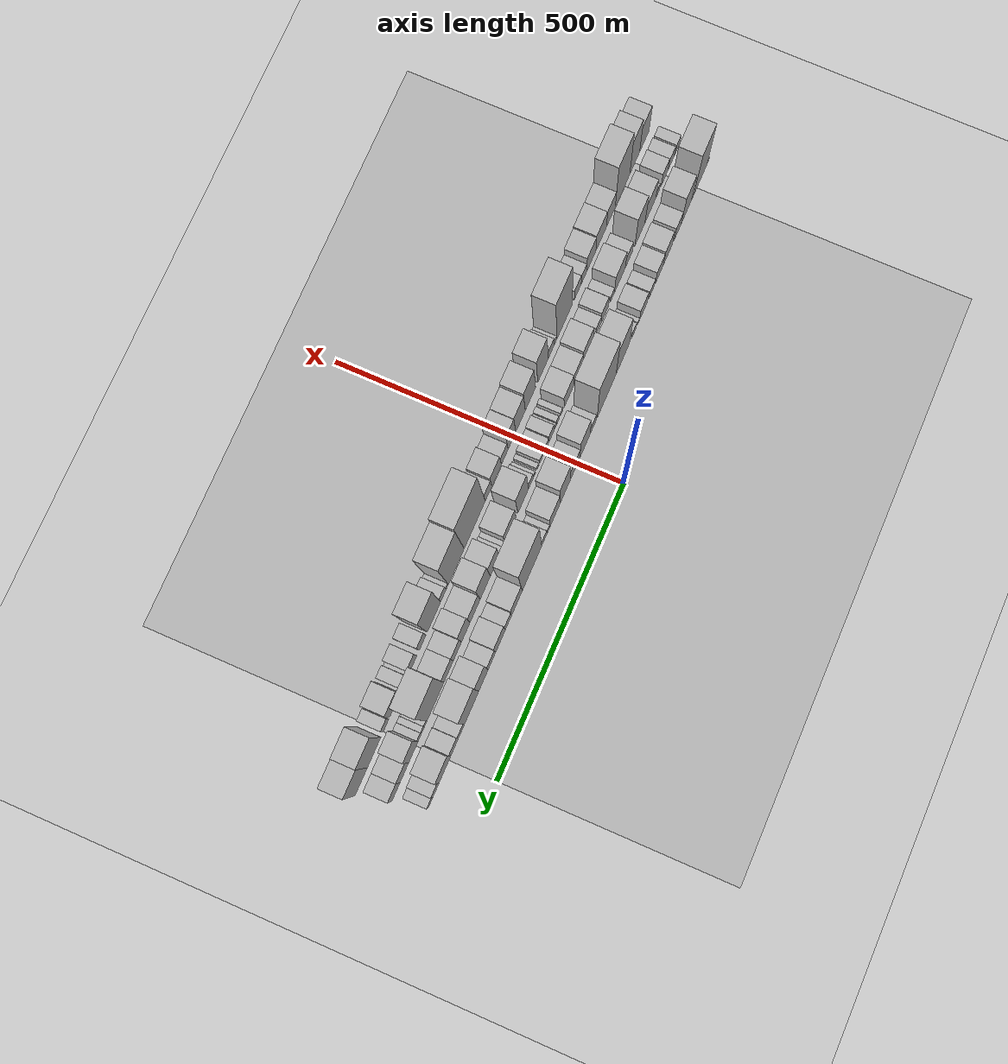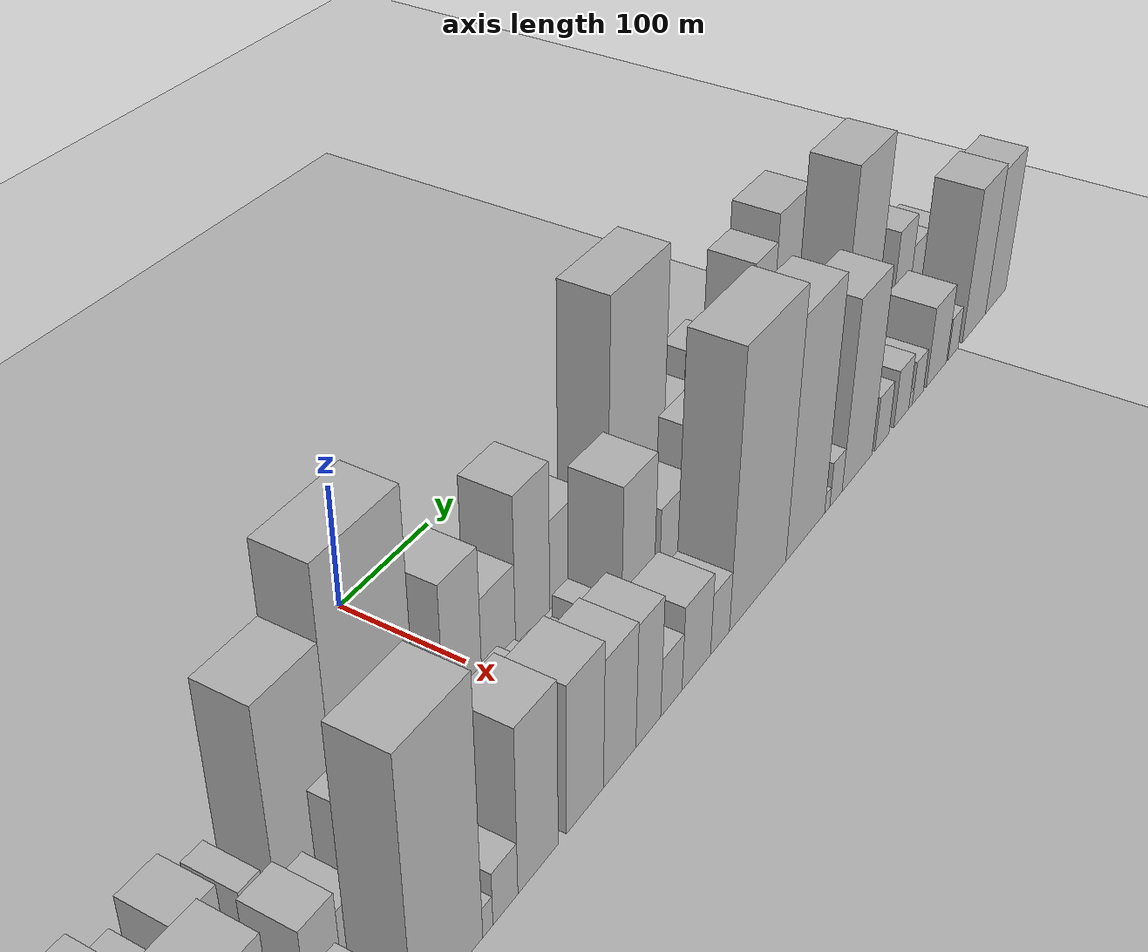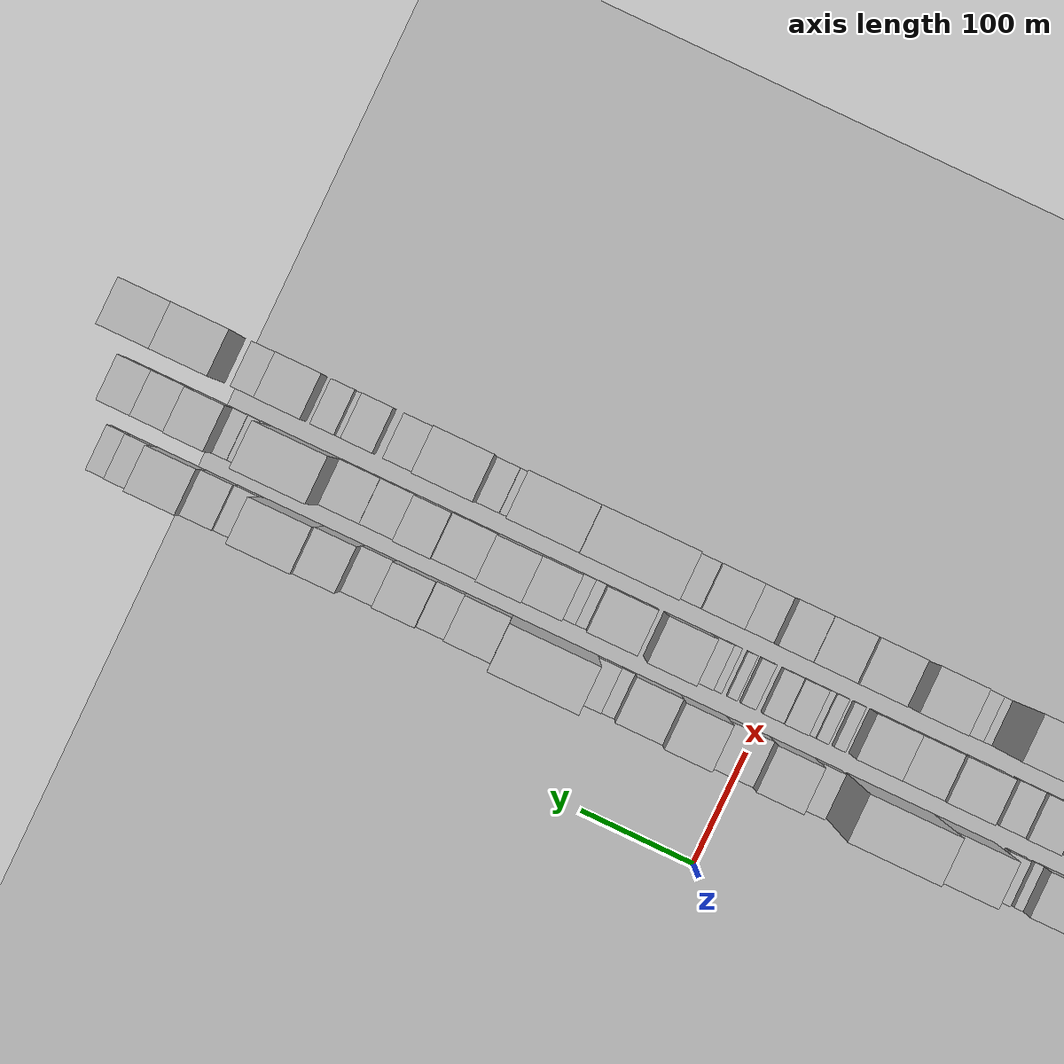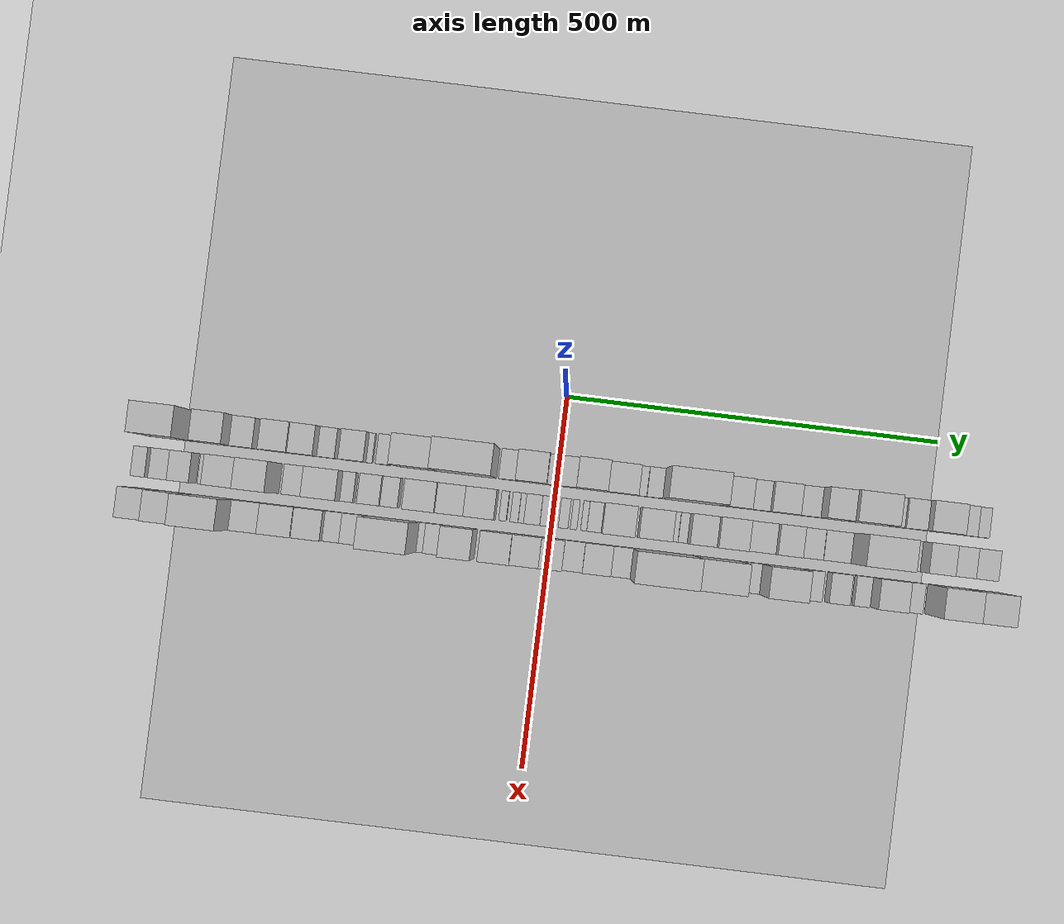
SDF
<?xml version="1.0" encoding="utf-8"?>

<sdf version="1.6">

   <world name="default">

      <gui fullscreen="0">

         <camera name="user_camera">

            <pose>-15 0 4.57585 0 0 0</pose>

            <view_controller>orbit</view_controller>

         </camera>

      </gui>

      <scene>

         <sky>

           <clouds>

             <speed>12</speed>

           </clouds>

         </sky>

         <ambient>0.4 0.4 0.4 1</ambient>

         <background>0.7 0.7 0.7 1</background>

         <shadows>1</shadows>

      </scene>

      <gravity>0 0 -9.8066</gravity>

      <magnetic_field>6e-06 2.3e-05 -4.2e-05</magnetic_field>

      <physics default="0" name="default_physics" type="ode">

         <ode>

            <solver>

               <type>quick</type>

               <iters>10</iters>

               <sor>1.0</sor>

               <use_dynamic_moi_rescaling>0</use_dynamic_moi_rescaling>

            </solver>

            <constraints>

               <cfm>0</cfm>

               <erp>0.2</erp>

               <contact_max_correcting_vel>100</contact_max_correcting_vel>

               <contact_surface_layer>0.001</contact_surface_layer>

            </constraints>

         </ode>

         <max_step_size>0.004</max_step_size>

         <real_time_factor>1</real_time_factor>

         <real_time_update_rate>250</real_time_update_rate>

      </physics>

      <light name="sun" type="directional">

         <cast_shadows>1</cast_shadows>

         <pose>0 0 10 0 0 0</pose>

         <diffuse>0.8 0.8 0.8 1</diffuse>

         <specular>0.2 0.2 0.2 1</specular>

         <attenuation>

            <range>1000</range>

            <constant>0.9</constant>

            <linear>0.01</linear>

            <quadratic>0.001</quadratic>

         </attenuation>

         <direction>-0.5 0.1 -0.9</direction>

      </light>

      <include>

         <name>ground_plane_1</name>

         <uri>model://HANNAS_ground_plane</uri>

         <pose>0 0 0  0 0 0</pose>

      </include>

      <include>

         <name>ground_plane_2</name>

         <uri>model://HANNAS_ground_plane</uri>

         <pose>100 0 0  0 0 0</pose>

      </include>

      <model name="building_1">

         <static>1</static>

         <pose frame="">100.0000 -546.8630 0 0.000000 0.000000 0.000000</pose>

         <link name="link">

            <pose frame="">0 0 9.00 0 0 0</pose>

            <collision name="collision">

               <geometry>

                  <box>

                     <size>40.0000 8.2741 18.0000</size>

                  </box>

               </geometry>

               <max_contacts>10</max_contacts>

               <surface>

                  <contact>

                     <ode/>

                  </contact>

                  <bounce/>

                  <friction>

                     <torsional>

                        <ode/>

                     </torsional>

                     <ode/>

                  </friction>

               </surface>

            </collision>

            <visual name="visual">

               <cast_shadows>0</cast_shadows>

               <geometry>

                  <box>

                     <size>40.0000 8.2741 18.0000</size>

                  </box>

               </geometry>

               <material>

                  <script>

                     <uri>model://HANNAS_wall/materials/scripts</uri>

                     <uri>model://HANNAS_wall/materials/textures</uri>

                     <name>vrc/HANNAS_wall</name>

                  </script>

               </material>

            </visual>

            <self_collide>0</self_collide>

            <enable_wind>0</enable_wind>

            <kinematic>0</kinematic>

         </link>

      </model>

      <model name="building_2">

         <static>1</static>

         <pose frame="">100.0000 -513.9525 0 0.000000 0.000000 0.000000</pose>

         <link name="link">

            <pose frame="">0 0 85.50 0 0 0</pose>

            <collision name="collision">

               <geometry>

                  <box>

                     <size>40.0000 57.5469 171.0000</size>

                  </box>

               </geometry>

               <max_contacts>10</max_contacts>

               <surface>

                  <contact>

                     <ode/>

                  </contact>

                  <bounce/>

                  <friction>

                     <torsional>

                        <ode/>

                     </torsional>

                     <ode/>

                  </friction>

               </surface>

            </collision>

            <visual name="visual">

               <cast_shadows>0</cast_shadows>

               <geometry>

                  <box>

                     <size>40.0000 57.5469 171.0000</size>

                  </box>

               </geometry>

               <material>

                  <script>

                     <uri>model://HANNAS_wall/materials/scripts</uri>

                     <uri>model://HANNAS_wall/materials/textures</uri>

                     <name>vrc/HANNAS_wall</name>

                  </script>

               </material>

            </visual>

            <self_collide>0</self_collide>

            <enable_wind>0</enable_wind>

            <kinematic>0</kinematic>

         </link>

      </model>

      <model name="building_3">

         <static>1</static>

         <pose frame="">100.0000 -480.7667 0 0.000000 0.000000 0.000000</pose>

         <link name="link">

            <pose frame="">0 0 9.00 0 0 0</pose>

            <collision name="collision">

               <geometry>

                  <box>

                     <size>40.0000 8.8247 18.0000</size>

                  </box>

               </geometry>

               <max_contacts>10</max_contacts>

               <surface>

                  <contact>

                     <ode/>

                  </contact>

                  <bounce/>

                  <friction>

                     <torsional>

                        <ode/>

                     </torsional>

                     <ode/>

                  </friction>

               </surface>

            </collision>

            <visual name="visual">

               <cast_shadows>0</cast_shadows>

               <geometry>

                  <box>

                     <size>40.0000 8.8247 18.0000</size>

                  </box>

               </geometry>

               <material>

                  <script>

                     <uri>model://HANNAS_wall/materials/scripts</uri>

                     <uri>model://HANNAS_wall/materials/textures</uri>

                     <name>vrc/HANNAS_wall</name>

                  </script>

               </material>

            </visual>

            <self_collide>0</self_collide>

            <enable_wind>0</enable_wind>

            <kinematic>0</kinematic>

         </link>

      </model>

      <model name="building_4">

         <static>1</static>

         <pose frame="">100.0000 -452.3800 0 0.000000 0.000000 0.000000</pose>

         <link name="link">

            <pose frame="">0 0 60.00 0 0 0</pose>

            <collision name="collision">

               <geometry>

                  <box>

                     <size>40.0000 41.9488 120.0000</size>

                  </box>

               </geometry>

               <max_contacts>10</max_contacts>

               <surface>

                  <contact>

                     <ode/>

                  </contact>

                  <bounce/>

                  <friction>

                     <torsional>

                        <ode/>

                     </torsional>

                     <ode/>

                  </friction>

               </surface>

            </collision>

            <visual name="visual">

               <cast_shadows>0</cast_shadows>

               <geometry>

                  <box>

                     <size>40.0000 41.9488 120.0000</size>

                  </box>

               </geometry>

               <material>

                  <script>

                     <uri>model://HANNAS_wall/materials/scripts</uri>

                     <uri>model://HANNAS_wall/materials/textures</uri>

                     <name>vrc/HANNAS_wall</name>

                  </script>

               </material>

            </visual>

            <self_collide>0</self_collide>

            <enable_wind>0</enable_wind>

            <kinematic>0</kinematic>

         </link>

      </model>

      <model name="building_5">

         <static>1</static>

         <pose frame="">100.0000 -416.2095 0 0.000000 0.000000 0.000000</pose>

         <link name="link">

            <pose frame="">0 0 30.00 0 0 0</pose>

            <collision name="collision">

               <geometry>

                  <box>

                     <size>40.0000 30.3921 60.0000</size>

                  </box>

               </geometry>

               <max_contacts>10</max_contacts>

               <surface>

                  <contact>

                     <ode/>

                  </contact>

                  <bounce/>

                  <friction>

                     <torsional>

                        <ode/>

                     </torsional>

                     <ode/>

                  </friction>

               </surface>

            </collision>

            <visual name="visual">

               <cast_shadows>0</cast_shadows>

               <geometry>

                  <box>

                     <size>40.0000 30.3921 60.0000</size>

                  </box>

               </geometry>

               <material>

                  <script>

                     <uri>model://HANNAS_wall/materials/scripts</uri>

                     <uri>model://HANNAS_wall/materials/textures</uri>

                     <name>vrc/HANNAS_wall</name>

                  </script>

               </material>

            </visual>

            <self_collide>0</self_collide>

            <enable_wind>0</enable_wind>

            <kinematic>0</kinematic>

         </link>

      </model>

      <model name="building_6">

         <static>1</static>

         <pose frame="">100.0000 -373.3423 0 0.000000 0.000000 0.000000</pose>

         <link name="link">

            <pose frame="">0 0 36.00 0 0 0</pose>

            <collision name="collision">

               <geometry>

                  <box>

                     <size>40.0000 37.3423 72.0000</size>

                  </box>

               </geometry>

               <max_contacts>10</max_contacts>

               <surface>

                  <contact>

                     <ode/>

                  </contact>

                  <bounce/>

                  <friction>

                     <torsional>

                        <ode/>

                     </torsional>

                     <ode/>

                  </friction>

               </surface>

            </collision>

            <visual name="visual">

               <cast_shadows>0</cast_shadows>

               <geometry>

                  <box>

                     <size>40.0000 37.3423 72.0000</size>

                  </box>

               </geometry>

               <material>

                  <script>

                     <uri>model://HANNAS_wall/materials/scripts</uri>

                     <uri>model://HANNAS_wall/materials/textures</uri>

                     <name>vrc/HANNAS_wall</name>

                  </script>

               </material>

            </visual>

            <self_collide>0</self_collide>

            <enable_wind>0</enable_wind>

            <kinematic>0</kinematic>

         </link>

      </model>

      <model name="building_7">

         <static>1</static>

         <pose frame="">100.0000 -337.8517 0 0.000000 0.000000 0.000000</pose>

         <link name="link">

            <pose frame="">0 0 31.50 0 0 0</pose>

            <collision name="collision">

               <geometry>

                  <box>

                     <size>40.0000 33.6390 63.0000</size>

                  </box>

               </geometry>

               <max_contacts>10</max_contacts>

               <surface>

                  <contact>

                     <ode/>

                  </contact>

                  <bounce/>

                  <friction>

                     <torsional>

                        <ode/>

                     </torsional>

                     <ode/>

                  </friction>

               </surface>

            </collision>

            <visual name="visual">

               <cast_shadows>0</cast_shadows>

               <geometry>

                  <box>

                     <size>40.0000 33.6390 63.0000</size>

                  </box>

               </geometry>

               <material>

                  <script>

                     <uri>model://HANNAS_wall/materials/scripts</uri>

                     <uri>model://HANNAS_wall/materials/textures</uri>

                     <name>vrc/HANNAS_wall</name>

                  </script>

               </material>

            </visual>

            <self_collide>0</self_collide>

            <enable_wind>0</enable_wind>

            <kinematic>0</kinematic>

         </link>

      </model>

      <model name="building_8">

         <static>1</static>

         <pose frame="">100.0000 -306.4036 0 0.000000 0.000000 0.000000</pose>

         <link name="link">

            <pose frame="">0 0 19.50 0 0 0</pose>

            <collision name="collision">

               <geometry>

                  <box>

                     <size>40.0000 23.2571 39.0000</size>

                  </box>

               </geometry>

               <max_contacts>10</max_contacts>

               <surface>

                  <contact>

                     <ode/>

                  </contact>

                  <bounce/>

                  <friction>

                     <torsional>

                        <ode/>

                     </torsional>

                     <ode/>

                  </friction>

               </surface>

            </collision>

            <visual name="visual">

               <cast_shadows>0</cast_shadows>

               <geometry>

                  <box>

                     <size>40.0000 23.2571 39.0000</size>

                  </box>

               </geometry>

               <material>

                  <script>

                     <uri>model://HANNAS_wall/materials/scripts</uri>

                     <uri>model://HANNAS_wall/materials/textures</uri>

                     <name>vrc/HANNAS_wall</name>

                  </script>

               </material>

            </visual>

            <self_collide>0</self_collide>

            <enable_wind>0</enable_wind>

            <kinematic>0</kinematic>

         </link>

      </model>

      <model name="building_9">

         <static>1</static>

         <pose frame="">100.0000 -271.2028 0 0.000000 0.000000 0.000000</pose>

         <link name="link">

            <pose frame="">0 0 28.50 0 0 0</pose>

            <collision name="collision">

               <geometry>

                  <box>

                     <size>40.0000 33.1445 57.0000</size>

                  </box>

               </geometry>

               <max_contacts>10</max_contacts>

               <surface>

                  <contact>

                     <ode/>

                  </contact>

                  <bounce/>

                  <friction>

                     <torsional>

                        <ode/>

                     </torsional>

                     <ode/>

                  </friction>

               </surface>

            </collision>

            <visual name="visual">

               <cast_shadows>0</cast_shadows>

               <geometry>

                  <box>

                     <size>40.0000 33.1445 57.0000</size>

                  </box>

               </geometry>

               <material>

                  <script>

                     <uri>model://HANNAS_wall/materials/scripts</uri>

                     <uri>model://HANNAS_wall/materials/textures</uri>

                     <name>vrc/HANNAS_wall</name>

                  </script>

               </material>

            </visual>

            <self_collide>0</self_collide>

            <enable_wind>0</enable_wind>

            <kinematic>0</kinematic>

         </link>

      </model>

      <model name="building_10">

         <static>1</static>

         <pose frame="">100.0000 -250.5992 0 0.000000 0.000000 0.000000</pose>

         <link name="link">

            <pose frame="">0 0 9.00 0 0 0</pose>

            <collision name="collision">

               <geometry>

                  <box>

                     <size>40.0000 8.0627 18.0000</size>

                  </box>

               </geometry>

               <max_contacts>10</max_contacts>

               <surface>

                  <contact>

                     <ode/>

                  </contact>

                  <bounce/>

                  <friction>

                     <torsional>

                        <ode/>

                     </torsional>

                     <ode/>

                  </friction>

               </surface>

            </collision>

            <visual name="visual">

               <cast_shadows>0</cast_shadows>

               <geometry>

                  <box>

                     <size>40.0000 8.0627 18.0000</size>

                  </box>

               </geometry>

               <material>

                  <script>

                     <uri>model://HANNAS_wall/materials/scripts</uri>

                     <uri>model://HANNAS_wall/materials/textures</uri>

                     <name>vrc/HANNAS_wall</name>

                  </script>

               </material>

            </visual>

            <self_collide>0</self_collide>

            <enable_wind>0</enable_wind>

            <kinematic>0</kinematic>

         </link>

      </model>

      <model name="building_11">

         <static>1</static>

         <pose frame="">100.0000 -231.4067 0 0.000000 0.000000 0.000000</pose>

         <link name="link">

            <pose frame="">0 0 18.00 0 0 0</pose>

            <collision name="collision">

               <geometry>

                  <box>

                     <size>40.0000 18.3222 36.0000</size>

                  </box>

               </geometry>

               <max_contacts>10</max_contacts>

               <surface>

                  <contact>

                     <ode/>

                  </contact>

                  <bounce/>

                  <friction>

                     <torsional>

                        <ode/>

                     </torsional>

                     <ode/>

                  </friction>

               </surface>

            </collision>

            <visual name="visual">

               <cast_shadows>0</cast_shadows>

               <geometry>

                  <box>

                     <size>40.0000 18.3222 36.0000</size>

                  </box>

               </geometry>

               <material>

                  <script>

                     <uri>model://HANNAS_wall/materials/scripts</uri>

                     <uri>model://HANNAS_wall/materials/textures</uri>

                     <name>vrc/HANNAS_wall</name>

                  </script>

               </material>

            </visual>

            <self_collide>0</self_collide>

            <enable_wind>0</enable_wind>

            <kinematic>0</kinematic>

         </link>

      </model>

      <model name="building_12">

         <static>1</static>

         <pose frame="">100.0000 -185.6500 0 0.000000 0.000000 0.000000</pose>

         <link name="link">

            <pose frame="">0 0 75.00 0 0 0</pose>

            <collision name="collision">

               <geometry>

                  <box>

                     <size>40.0000 55.1913 150.0000</size>

                  </box>

               </geometry>

               <max_contacts>10</max_contacts>

               <surface>

                  <contact>

                     <ode/>

                  </contact>

                  <bounce/>

                  <friction>

                     <torsional>

                        <ode/>

                     </torsional>

                     <ode/>

                  </friction>

               </surface>

            </collision>

            <visual name="visual">

               <cast_shadows>0</cast_shadows>

               <geometry>

                  <box>

                     <size>40.0000 55.1913 150.0000</size>

                  </box>

               </geometry>

               <material>

                  <script>

                     <uri>model://HANNAS_wall/materials/scripts</uri>

                     <uri>model://HANNAS_wall/materials/textures</uri>

                     <name>vrc/HANNAS_wall</name>

                  </script>

               </material>

            </visual>

            <self_collide>0</self_collide>

            <enable_wind>0</enable_wind>

            <kinematic>0</kinematic>

         </link>

      </model>

      <model name="building_13">

         <static>1</static>

         <pose frame="">100.0000 -119.1153 0 0.000000 0.000000 0.000000</pose>

         <link name="link">

            <pose frame="">0 0 102.00 0 0 0</pose>

            <collision name="collision">

               <geometry>

                  <box>

                     <size>40.0000 77.8781 204.0000</size>

                  </box>

               </geometry>

               <max_contacts>10</max_contacts>

               <surface>

                  <contact>

                     <ode/>

                  </contact>

                  <bounce/>

                  <friction>

                     <torsional>

                        <ode/>

                     </torsional>

                     <ode/>

                  </friction>

               </surface>

            </collision>

            <visual name="visual">

               <cast_shadows>0</cast_shadows>

               <geometry>

                  <box>

                     <size>40.0000 77.8781 204.0000</size>

                  </box>

               </geometry>

               <material>

                  <script>

                     <uri>model://HANNAS_wall/materials/scripts</uri>

                     <uri>model://HANNAS_wall/materials/textures</uri>

                     <name>vrc/HANNAS_wall</name>

                  </script>

               </material>

            </visual>

            <self_collide>0</self_collide>

            <enable_wind>0</enable_wind>

            <kinematic>0</kinematic>

         </link>

      </model>

      <model name="building_14">

         <static>1</static>

         <pose frame="">100.0000 -64.1323 0 0.000000 0.000000 0.000000</pose>

         <link name="link">

            <pose frame="">0 0 22.50 0 0 0</pose>

            <collision name="collision">

               <geometry>

                  <box>

                     <size>40.0000 24.0878 45.0000</size>

                  </box>

               </geometry>

               <max_contacts>10</max_contacts>

               <surface>

                  <contact>

                     <ode/>

                  </contact>

                  <bounce/>

                  <friction>

                     <torsional>

                        <ode/>

                     </torsional>

                     <ode/>

                  </friction>

               </surface>

            </collision>

            <visual name="visual">

               <cast_shadows>0</cast_shadows>

               <geometry>

                  <box>

                     <size>40.0000 24.0878 45.0000</size>

                  </box>

               </geometry>

               <material>

                  <script>

                     <uri>model://HANNAS_wall/materials/scripts</uri>

                     <uri>model://HANNAS_wall/materials/textures</uri>

                     <name>vrc/HANNAS_wall</name>

                  </script>

               </material>

            </visual>

            <self_collide>0</self_collide>

            <enable_wind>0</enable_wind>

            <kinematic>0</kinematic>

         </link>

      </model>

      <model name="building_15">

         <static>1</static>

         <pose frame="">100.0000 -31.6384 0 0.000000 0.000000 0.000000</pose>

         <link name="link">

            <pose frame="">0 0 55.50 0 0 0</pose>

            <collision name="collision">

               <geometry>

                  <box>

                     <size>40.0000 40.9000 111.0000</size>

                  </box>

               </geometry>

               <max_contacts>10</max_contacts>

               <surface>

                  <contact>

                     <ode/>

                  </contact>

                  <bounce/>

                  <friction>

                     <torsional>

                        <ode/>

                     </torsional>

                     <ode/>

                  </friction>

               </surface>

            </collision>

            <visual name="visual">

               <cast_shadows>0</cast_shadows>

               <geometry>

                  <box>

                     <size>40.0000 40.9000 111.0000</size>

                  </box>

               </geometry>

               <material>

                  <script>

                     <uri>model://HANNAS_wall/materials/scripts</uri>

                     <uri>model://HANNAS_wall/materials/textures</uri>

                     <name>vrc/HANNAS_wall</name>

                  </script>

               </material>

            </visual>

            <self_collide>0</self_collide>

            <enable_wind>0</enable_wind>

            <kinematic>0</kinematic>

         </link>

      </model>

      <model name="building_16">

         <static>1</static>

         <pose frame="">100.0000 8.0737 0 0.000000 0.000000 0.000000</pose>

         <link name="link">

            <pose frame="">0 0 34.50 0 0 0</pose>

            <collision name="collision">

               <geometry>

                  <box>

                     <size>40.0000 38.5243 69.0000</size>

                  </box>

               </geometry>

               <max_contacts>10</max_contacts>

               <surface>

                  <contact>

                     <ode/>

                  </contact>

                  <bounce/>

                  <friction>

                     <torsional>

                        <ode/>

                     </torsional>

                     <ode/>

                  </friction>

               </surface>

            </collision>

            <visual name="visual">

               <cast_shadows>0</cast_shadows>

               <geometry>

                  <box>

                     <size>40.0000 38.5243 69.0000</size>

                  </box>

               </geometry>

               <material>

                  <script>

                     <uri>model://HANNAS_wall/materials/scripts</uri>

                     <uri>model://HANNAS_wall/materials/textures</uri>

                     <name>vrc/HANNAS_wall</name>

                  </script>

               </material>

            </visual>

            <self_collide>0</self_collide>

            <enable_wind>0</enable_wind>

            <kinematic>0</kinematic>

         </link>

      </model>

      <model name="building_17">

         <static>1</static>

         <pose frame="">100.0000 47.7928 0 0.000000 0.000000 0.000000</pose>

         <link name="link">

            <pose frame="">0 0 61.50 0 0 0</pose>

            <collision name="collision">

               <geometry>

                  <box>

                     <size>40.0000 40.9139 123.0000</size>

                  </box>

               </geometry>

               <max_contacts>10</max_contacts>

               <surface>

                  <contact>

                     <ode/>

                  </contact>

                  <bounce/>

                  <friction>

                     <torsional>

                        <ode/>

                     </torsional>

                     <ode/>

                  </friction>

               </surface>

            </collision>

            <visual name="visual">

               <cast_shadows>0</cast_shadows>

               <geometry>

                  <box>

                     <size>40.0000 40.9139 123.0000</size>

                  </box>

               </geometry>

               <material>

                  <script>

                     <uri>model://HANNAS_wall/materials/scripts</uri>

                     <uri>model://HANNAS_wall/materials/textures</uri>

                     <name>vrc/HANNAS_wall</name>

                  </script>

               </material>

            </visual>

            <self_collide>0</self_collide>

            <enable_wind>0</enable_wind>

            <kinematic>0</kinematic>

         </link>

      </model>

      <model name="building_18">

         <static>1</static>

         <pose frame="">100.0000 88.7634 0 0.000000 0.000000 0.000000</pose>

         <link name="link">

            <pose frame="">0 0 37.50 0 0 0</pose>

            <collision name="collision">

               <geometry>

                  <box>

                     <size>40.0000 41.0273 75.0000</size>

                  </box>

               </geometry>

               <max_contacts>10</max_contacts>

               <surface>

                  <contact>

                     <ode/>

                  </contact>

                  <bounce/>

                  <friction>

                     <torsional>

                        <ode/>

                     </torsional>

                     <ode/>

                  </friction>

               </surface>

            </collision>

            <visual name="visual">

               <cast_shadows>0</cast_shadows>

               <geometry>

                  <box>

                     <size>40.0000 41.0273 75.0000</size>

                  </box>

               </geometry>

               <material>

                  <script>

                     <uri>model://HANNAS_wall/materials/scripts</uri>

                     <uri>model://HANNAS_wall/materials/textures</uri>

                     <name>vrc/HANNAS_wall</name>

                  </script>

               </material>

            </visual>

            <self_collide>0</self_collide>

            <enable_wind>0</enable_wind>

            <kinematic>0</kinematic>

         </link>

      </model>

      <model name="building_19">

         <static>1</static>

         <pose frame="">100.0000 115.1914 0 0.000000 0.000000 0.000000</pose>

         <link name="link">

            <pose frame="">0 0 13.50 0 0 0</pose>

            <collision name="collision">

               <geometry>

                  <box>

                     <size>40.0000 11.8286 27.0000</size>

                  </box>

               </geometry>

               <max_contacts>10</max_contacts>

               <surface>

                  <contact>

                     <ode/>

                  </contact>

                  <bounce/>

                  <friction>

                     <torsional>

                        <ode/>

                     </torsional>

                     <ode/>

                  </friction>

               </surface>

            </collision>

            <visual name="visual">

               <cast_shadows>0</cast_shadows>

               <geometry>

                  <box>

                     <size>40.0000 11.8286 27.0000</size>

                  </box>

               </geometry>

               <material>

                  <script>

                     <uri>model://HANNAS_wall/materials/scripts</uri>

                     <uri>model://HANNAS_wall/materials/textures</uri>

                     <name>vrc/HANNAS_wall</name>

                  </script>

               </material>

            </visual>

            <self_collide>0</self_collide>

            <enable_wind>0</enable_wind>

            <kinematic>0</kinematic>

         </link>

      </model>

      <model name="building_20">

         <static>1</static>

         <pose frame="">100.0000 131.5545 0 0.000000 0.000000 0.000000</pose>

         <link name="link">

            <pose frame="">0 0 19.50 0 0 0</pose>

            <collision name="collision">

               <geometry>

                  <box>

                     <size>40.0000 20.8976 39.0000</size>

                  </box>

               </geometry>

               <max_contacts>10</max_contacts>

               <surface>

                  <contact>

                     <ode/>

                  </contact>

                  <bounce/>

                  <friction>

                     <torsional>

                        <ode/>

                     </torsional>

                     <ode/>

                  </friction>

               </surface>

            </collision>

            <visual name="visual">

               <cast_shadows>0</cast_shadows>

               <geometry>

                  <box>

                     <size>40.0000 20.8976 39.0000</size>

                  </box>

               </geometry>

               <material>

                  <script>

                     <uri>model://HANNAS_wall/materials/scripts</uri>

                     <uri>model://HANNAS_wall/materials/textures</uri>

                     <name>vrc/HANNAS_wall</name>

                  </script>

               </material>

            </visual>

            <self_collide>0</self_collide>

            <enable_wind>0</enable_wind>

            <kinematic>0</kinematic>

         </link>

      </model>

      <model name="building_21">

         <static>1</static>

         <pose frame="">100.0000 180.0972 0 0.000000 0.000000 0.000000</pose>

         <link name="link">

            <pose frame="">0 0 102.00 0 0 0</pose>

            <collision name="collision">

               <geometry>

                  <box>

                     <size>40.0000 76.1879 204.0000</size>

                  </box>

               </geometry>

               <max_contacts>10</max_contacts>

               <surface>

                  <contact>

                     <ode/>

                  </contact>

                  <bounce/>

                  <friction>

                     <torsional>

                        <ode/>

                     </torsional>

                     <ode/>

                  </friction>

               </surface>

            </collision>

            <visual name="visual">

               <cast_shadows>0</cast_shadows>

               <geometry>

                  <box>

                     <size>40.0000 76.1879 204.0000</size>

                  </box>

               </geometry>

               <material>

                  <script>

                     <uri>model://HANNAS_wall/materials/scripts</uri>

                     <uri>model://HANNAS_wall/materials/textures</uri>

                     <name>vrc/HANNAS_wall</name>

                  </script>

               </material>

            </visual>

            <self_collide>0</self_collide>

            <enable_wind>0</enable_wind>

            <kinematic>0</kinematic>

         </link>

      </model>

      <model name="building_22">

         <static>1</static>

         <pose frame="">100.0000 238.7869 0 0.000000 0.000000 0.000000</pose>

         <link name="link">

            <pose frame="">0 0 34.50 0 0 0</pose>

            <collision name="collision">

               <geometry>

                  <box>

                     <size>40.0000 41.1914 69.0000</size>

                  </box>

               </geometry>

               <max_contacts>10</max_contacts>

               <surface>

                  <contact>

                     <ode/>

                  </contact>

                  <bounce/>

                  <friction>

                     <torsional>

                        <ode/>

                     </torsional>

                     <ode/>

                  </friction>

               </surface>

            </collision>

            <visual name="visual">

               <cast_shadows>0</cast_shadows>

               <geometry>

                  <box>

                     <size>40.0000 41.1914 69.0000</size>

                  </box>

               </geometry>

               <material>

                  <script>

                     <uri>model://HANNAS_wall/materials/scripts</uri>

                     <uri>model://HANNAS_wall/materials/textures</uri>

                     <name>vrc/HANNAS_wall</name>

                  </script>

               </material>

            </visual>

            <self_collide>0</self_collide>

            <enable_wind>0</enable_wind>

            <kinematic>0</kinematic>

         </link>

      </model>

      <model name="building_23">

         <static>1</static>

         <pose frame="">100.0000 271.7643 0 0.000000 0.000000 0.000000</pose>

         <link name="link">

            <pose frame="">0 0 24.00 0 0 0</pose>

            <collision name="collision">

               <geometry>

                  <box>

                     <size>40.0000 24.7636 48.0000</size>

                  </box>

               </geometry>

               <max_contacts>10</max_contacts>

               <surface>

                  <contact>

                     <ode/>

                  </contact>

                  <bounce/>

                  <friction>

                     <torsional>

                        <ode/>

                     </torsional>

                     <ode/>

                  </friction>

               </surface>

            </collision>

            <visual name="visual">

               <cast_shadows>0</cast_shadows>

               <geometry>

                  <box>

                     <size>40.0000 24.7636 48.0000</size>

                  </box>

               </geometry>

               <material>

                  <script>

                     <uri>model://HANNAS_wall/materials/scripts</uri>

                     <uri>model://HANNAS_wall/materials/textures</uri>

                     <name>vrc/HANNAS_wall</name>

                  </script>

               </material>

            </visual>

            <self_collide>0</self_collide>

            <enable_wind>0</enable_wind>

            <kinematic>0</kinematic>

         </link>

      </model>

      <model name="building_24">

         <static>1</static>

         <pose frame="">100.0000 303.0075 0 0.000000 0.000000 0.000000</pose>

         <link name="link">

            <pose frame="">0 0 37.50 0 0 0</pose>

            <collision name="collision">

               <geometry>

                  <box>

                     <size>40.0000 37.7227 75.0000</size>

                  </box>

               </geometry>

               <max_contacts>10</max_contacts>

               <surface>

                  <contact>

                     <ode/>

                  </contact>

                  <bounce/>

                  <friction>

                     <torsional>

                        <ode/>

                     </torsional>

                     <ode/>

                  </friction>

               </surface>

            </collision>

            <visual name="visual">

               <cast_shadows>0</cast_shadows>

               <geometry>

                  <box>

                     <size>40.0000 37.7227 75.0000</size>

                  </box>

               </geometry>

               <material>

                  <script>

                     <uri>model://HANNAS_wall/materials/scripts</uri>

                     <uri>model://HANNAS_wall/materials/textures</uri>

                     <name>vrc/HANNAS_wall</name>

                  </script>

               </material>

            </visual>

            <self_collide>0</self_collide>

            <enable_wind>0</enable_wind>

            <kinematic>0</kinematic>

         </link>

      </model>

      <model name="building_25">

         <static>1</static>

         <pose frame="">100.0000 336.1396 0 0.000000 0.000000 0.000000</pose>

         <link name="link">

            <pose frame="">0 0 25.50 0 0 0</pose>

            <collision name="collision">

               <geometry>

                  <box>

                     <size>40.0000 28.5414 51.0000</size>

                  </box>

               </geometry>

               <max_contacts>10</max_contacts>

               <surface>

                  <contact>

                     <ode/>

                  </contact>

                  <bounce/>

                  <friction>

                     <torsional>

                        <ode/>

                     </torsional>

                     <ode/>

                  </friction>

               </surface>

            </collision>

            <visual name="visual">

               <cast_shadows>0</cast_shadows>

               <geometry>

                  <box>

                     <size>40.0000 28.5414 51.0000</size>

                  </box>

               </geometry>

               <material>

                  <script>

                     <uri>model://HANNAS_wall/materials/scripts</uri>

                     <uri>model://HANNAS_wall/materials/textures</uri>

                     <name>vrc/HANNAS_wall</name>

                  </script>

               </material>

            </visual>

            <self_collide>0</self_collide>

            <enable_wind>0</enable_wind>

            <kinematic>0</kinematic>

         </link>

      </model>

      <model name="building_26">

         <static>1</static>

         <pose frame="">100.0000 368.4329 0 0.000000 0.000000 0.000000</pose>

         <link name="link">

            <pose frame="">0 0 60.00 0 0 0</pose>

            <collision name="collision">

               <geometry>

                  <box>

                     <size>40.0000 36.0453 120.0000</size>

                  </box>

               </geometry>

               <max_contacts>10</max_contacts>

               <surface>

                  <contact>

                     <ode/>

                  </contact>

                  <bounce/>

                  <friction>

                     <torsional>

                        <ode/>

                     </torsional>

                     <ode/>

                  </friction>

               </surface>

            </collision>

            <visual name="visual">

               <cast_shadows>0</cast_shadows>

               <geometry>

                  <box>

                     <size>40.0000 36.0453 120.0000</size>

                  </box>

               </geometry>

               <material>

                  <script>

                     <uri>model://HANNAS_wall/materials/scripts</uri>

                     <uri>model://HANNAS_wall/materials/textures</uri>

                     <name>vrc/HANNAS_wall</name>

                  </script>

               </material>

            </visual>

            <self_collide>0</self_collide>

            <enable_wind>0</enable_wind>

            <kinematic>0</kinematic>

         </link>

      </model>

      <model name="building_27">

         <static>1</static>

         <pose frame="">100.0000 413.7367 0 0.000000 0.000000 0.000000</pose>

         <link name="link">

            <pose frame="">0 0 72.00 0 0 0</pose>

            <collision name="collision">

               <geometry>

                  <box>

                     <size>40.0000 54.5623 144.0000</size>

                  </box>

               </geometry>

               <max_contacts>10</max_contacts>

               <surface>

                  <contact>

                     <ode/>

                  </contact>

                  <bounce/>

                  <friction>

                     <torsional>

                        <ode/>

                     </torsional>

                     <ode/>

                  </friction>

               </surface>

            </collision>

            <visual name="visual">

               <cast_shadows>0</cast_shadows>

               <geometry>

                  <box>

                     <size>40.0000 54.5623 144.0000</size>

                  </box>

               </geometry>

               <material>

                  <script>

                     <uri>model://HANNAS_wall/materials/scripts</uri>

                     <uri>model://HANNAS_wall/materials/textures</uri>

                     <name>vrc/HANNAS_wall</name>

                  </script>

               </material>

            </visual>

            <self_collide>0</self_collide>

            <enable_wind>0</enable_wind>

            <kinematic>0</kinematic>

         </link>

      </model>

      <model name="building_28">

         <static>1</static>

         <pose frame="">100.0000 452.2882 0 0.000000 0.000000 0.000000</pose>

         <link name="link">

            <pose frame="">0 0 19.50 0 0 0</pose>

            <collision name="collision">

               <geometry>

                  <box>

                     <size>40.0000 22.5407 39.0000</size>

                  </box>

               </geometry>

               <max_contacts>10</max_contacts>

               <surface>

                  <contact>

                     <ode/>

                  </contact>

                  <bounce/>

                  <friction>

                     <torsional>

                        <ode/>

                     </torsional>

                     <ode/>

                  </friction>

               </surface>

            </collision>

            <visual name="visual">

               <cast_shadows>0</cast_shadows>

               <geometry>

                  <box>

                     <size>40.0000 22.5407 39.0000</size>

                  </box>

               </geometry>

               <material>

                  <script>

                     <uri>model://HANNAS_wall/materials/scripts</uri>

                     <uri>model://HANNAS_wall/materials/textures</uri>

                     <name>vrc/HANNAS_wall</name>

                  </script>

               </material>

            </visual>

            <self_collide>0</self_collide>

            <enable_wind>0</enable_wind>

            <kinematic>0</kinematic>

         </link>

      </model>

      <model name="building_29">

         <static>1</static>

         <pose frame="">100.0000 477.8087 0 0.000000 0.000000 0.000000</pose>

         <link name="link">

            <pose frame="">0 0 25.50 0 0 0</pose>

            <collision name="collision">

               <geometry>

                  <box>

                     <size>40.0000 28.5004 51.0000</size>

                  </box>

               </geometry>

               <max_contacts>10</max_contacts>

               <surface>

                  <contact>

                     <ode/>

                  </contact>

                  <bounce/>

                  <friction>

                     <torsional>

                        <ode/>

                     </torsional>

                     <ode/>

                  </friction>

               </surface>

            </collision>

            <visual name="visual">

               <cast_shadows>0</cast_shadows>

               <geometry>

                  <box>

                     <size>40.0000 28.5004 51.0000</size>

                  </box>

               </geometry>

               <material>

                  <script>

                     <uri>model://HANNAS_wall/materials/scripts</uri>

                     <uri>model://HANNAS_wall/materials/textures</uri>

                     <name>vrc/HANNAS_wall</name>

                  </script>

               </material>

            </visual>

            <self_collide>0</self_collide>

            <enable_wind>0</enable_wind>

            <kinematic>0</kinematic>

         </link>

      </model>

      <model name="building_30">

         <static>1</static>

         <pose frame="">100.0000 514.2186 0 0.000000 0.000000 0.000000</pose>

         <link name="link">

            <pose frame="">0 0 42.00 0 0 0</pose>

            <collision name="collision">

               <geometry>

                  <box>

                     <size>40.0000 44.3194 84.0000</size>

                  </box>

               </geometry>

               <max_contacts>10</max_contacts>

               <surface>

                  <contact>

                     <ode/>

                  </contact>

                  <bounce/>

                  <friction>

                     <torsional>

                        <ode/>

                     </torsional>

                     <ode/>

                  </friction>

               </surface>

            </collision>

            <visual name="visual">

               <cast_shadows>0</cast_shadows>

               <geometry>

                  <box>

                     <size>40.0000 44.3194 84.0000</size>

                  </box>

               </geometry>

               <material>

                  <script>

                     <uri>model://HANNAS_wall/materials/scripts</uri>

                     <uri>model://HANNAS_wall/materials/textures</uri>

                     <name>vrc/HANNAS_wall</name>

                  </script>

               </material>

            </visual>

            <self_collide>0</self_collide>

            <enable_wind>0</enable_wind>

            <kinematic>0</kinematic>

         </link>

      </model>

      <model name="building_31">

         <static>1</static>

         <pose frame="">100.0000 548.1095 0 0.000000 0.000000 0.000000</pose>

         <link name="link">

            <pose frame="">0 0 21.00 0 0 0</pose>

            <collision name="collision">

               <geometry>

                  <box>

                     <size>40.0000 23.4623 42.0000</size>

                  </box>

               </geometry>

               <max_contacts>10</max_contacts>

               <surface>

                  <contact>

                     <ode/>

                  </contact>

                  <bounce/>

                  <friction>

                     <torsional>

                        <ode/>

                     </torsional>

                     <ode/>

                  </friction>

               </surface>

            </collision>

            <visual name="visual">

               <cast_shadows>0</cast_shadows>

               <geometry>

                  <box>

                     <size>40.0000 23.4623 42.0000</size>

                  </box>

               </geometry>

               <material>

                  <script>

                     <uri>model://HANNAS_wall/materials/scripts</uri>

                     <uri>model://HANNAS_wall/materials/textures</uri>

                     <name>vrc/HANNAS_wall</name>

                  </script>

               </material>

            </visual>

            <self_collide>0</self_collide>

            <enable_wind>0</enable_wind>

            <kinematic>0</kinematic>

         </link>

      </model>

      <model name="building_32">

         <static>1</static>

         <pose frame="">100.0000 568.7242 0 0.000000 0.000000 0.000000</pose>

         <link name="link">

            <pose frame="">0 0 15.00 0 0 0</pose>

            <collision name="collision">

               <geometry>

                  <box>

                     <size>40.0000 17.7671 30.0000</size>

                  </box>

               </geometry>

               <max_contacts>10</max_contacts>

               <surface>

                  <contact>

                     <ode/>

                  </contact>

                  <bounce/>

                  <friction>

                     <torsional>

                        <ode/>

                     </torsional>

                     <ode/>

                  </friction>

               </surface>

            </collision>

            <visual name="visual">

               <cast_shadows>0</cast_shadows>

               <geometry>

                  <box>

                     <size>40.0000 17.7671 30.0000</size>

                  </box>

               </geometry>

               <material>

                  <script>

                     <uri>model://HANNAS_wall/materials/scripts</uri>

                     <uri>model://HANNAS_wall/materials/textures</uri>

                     <name>vrc/HANNAS_wall</name>

                  </script>

               </material>

            </visual>

            <self_collide>0</self_collide>

            <enable_wind>0</enable_wind>

            <kinematic>0</kinematic>

         </link>

      </model>

      <model name="building_33">

         <static>1</static>

         <pose frame="">155.0000 -550.4783 0 0.000000 0.000000 0.000000</pose>

         <link name="link">

            <pose frame="">0 0 18.00 0 0 0</pose>

            <collision name="collision">

               <geometry>

                  <box>

                     <size>40.0000 19.0434 36.0000</size>

                  </box>

               </geometry>

               <max_contacts>10</max_contacts>

               <surface>

                  <contact>

                     <ode/>

                  </contact>

                  <bounce/>

                  <friction>

                     <torsional>

                        <ode/>

                     </torsional>

                     <ode/>

                  </friction>

               </surface>

            </collision>

            <visual name="visual">

               <cast_shadows>0</cast_shadows>

               <geometry>

                  <box>

                     <size>40.0000 19.0434 36.0000</size>

                  </box>

               </geometry>

               <material>

                  <script>

                     <uri>model://HANNAS_wall/materials/scripts</uri>

                     <uri>model://HANNAS_wall/materials/textures</uri>

                     <name>vrc/HANNAS_wall</name>

                  </script>

               </material>

            </visual>

            <self_collide>0</self_collide>

            <enable_wind>0</enable_wind>

            <kinematic>0</kinematic>

         </link>

      </model>

      <model name="building_34">

         <static>1</static>

         <pose frame="">155.0000 -537.7247 0 0.000000 0.000000 0.000000</pose>

         <link name="link">

            <pose frame="">0 0 7.50 0 0 0</pose>

            <collision name="collision">

               <geometry>

                  <box>

                     <size>40.0000 6.4638 15.0000</size>

                  </box>

               </geometry>

               <max_contacts>10</max_contacts>

               <surface>

                  <contact>

                     <ode/>

                  </contact>

                  <bounce/>

                  <friction>

                     <torsional>

                        <ode/>

                     </torsional>

                     <ode/>

                  </friction>

               </surface>

            </collision>

            <visual name="visual">

               <cast_shadows>0</cast_shadows>

               <geometry>

                  <box>

                     <size>40.0000 6.4638 15.0000</size>

                  </box>

               </geometry>

               <material>

                  <script>

                     <uri>model://HANNAS_wall/materials/scripts</uri>

                     <uri>model://HANNAS_wall/materials/textures</uri>

                     <name>vrc/HANNAS_wall</name>

                  </script>

               </material>

            </visual>

            <self_collide>0</self_collide>

            <enable_wind>0</enable_wind>

            <kinematic>0</kinematic>

         </link>

      </model>

      <model name="building_35">

         <static>1</static>

         <pose frame="">155.0000 -521.3040 0 0.000000 0.000000 0.000000</pose>

         <link name="link">

            <pose frame="">0 0 22.50 0 0 0</pose>

            <collision name="collision">

               <geometry>

                  <box>

                     <size>40.0000 26.3776 45.0000</size>

                  </box>

               </geometry>

               <max_contacts>10</max_contacts>

               <surface>

                  <contact>

                     <ode/>

                  </contact>

                  <bounce/>

                  <friction>

                     <torsional>

                        <ode/>

                     </torsional>

                     <ode/>

                  </friction>

               </surface>

            </collision>

            <visual name="visual">

               <cast_shadows>0</cast_shadows>

               <geometry>

                  <box>

                     <size>40.0000 26.3776 45.0000</size>

                  </box>

               </geometry>

               <material>

                  <script>

                     <uri>model://HANNAS_wall/materials/scripts</uri>

                     <uri>model://HANNAS_wall/materials/textures</uri>

                     <name>vrc/HANNAS_wall</name>

                  </script>

               </material>

            </visual>

            <self_collide>0</self_collide>

            <enable_wind>0</enable_wind>

            <kinematic>0</kinematic>

         </link>

      </model>

      <model name="building_36">

         <static>1</static>

         <pose frame="">155.0000 -493.5138 0 0.000000 0.000000 0.000000</pose>

         <link name="link">

            <pose frame="">0 0 27.00 0 0 0</pose>

            <collision name="collision">

               <geometry>

                  <box>

                     <size>40.0000 29.2029 54.0000</size>

                  </box>

               </geometry>

               <max_contacts>10</max_contacts>

               <surface>

                  <contact>

                     <ode/>

                  </contact>

                  <bounce/>

                  <friction>

                     <torsional>

                        <ode/>

                     </torsional>

                     <ode/>

                  </friction>

               </surface>

            </collision>

            <visual name="visual">

               <cast_shadows>0</cast_shadows>

               <geometry>

                  <box>

                     <size>40.0000 29.2029 54.0000</size>

                  </box>

               </geometry>

               <material>

                  <script>

                     <uri>model://HANNAS_wall/materials/scripts</uri>

                     <uri>model://HANNAS_wall/materials/textures</uri>

                     <name>vrc/HANNAS_wall</name>

                  </script>

               </material>

            </visual>

            <self_collide>0</self_collide>

            <enable_wind>0</enable_wind>

            <kinematic>0</kinematic>

         </link>

      </model>

      <model name="building_37">

         <static>1</static>

         <pose frame="">155.0000 -464.1807 0 0.000000 0.000000 0.000000</pose>

         <link name="link">

            <pose frame="">0 0 15.00 0 0 0</pose>

            <collision name="collision">

               <geometry>

                  <box>

                     <size>40.0000 15.4633 30.0000</size>

                  </box>

               </geometry>

               <max_contacts>10</max_contacts>

               <surface>

                  <contact>

                     <ode/>

                  </contact>

                  <bounce/>

                  <friction>

                     <torsional>

                        <ode/>

                     </torsional>

                     <ode/>

                  </friction>

               </surface>

            </collision>

            <visual name="visual">

               <cast_shadows>0</cast_shadows>

               <geometry>

                  <box>

                     <size>40.0000 15.4633 30.0000</size>

                  </box>

               </geometry>

               <material>

                  <script>

                     <uri>model://HANNAS_wall/materials/scripts</uri>

                     <uri>model://HANNAS_wall/materials/textures</uri>

                     <name>vrc/HANNAS_wall</name>

                  </script>

               </material>

            </visual>

            <self_collide>0</self_collide>

            <enable_wind>0</enable_wind>

            <kinematic>0</kinematic>

         </link>

      </model>

      <model name="building_38">

         <static>1</static>

         <pose frame="">155.0000 -433.0651 0 0.000000 0.000000 0.000000</pose>

         <link name="link">

            <pose frame="">0 0 43.50 0 0 0</pose>

            <collision name="collision">

               <geometry>

                  <box>

                     <size>40.0000 46.7678 87.0000</size>

                  </box>

               </geometry>

               <max_contacts>10</max_contacts>

               <surface>

                  <contact>

                     <ode/>

                  </contact>

                  <bounce/>

                  <friction>

                     <torsional>

                        <ode/>

                     </torsional>

                     <ode/>

                  </friction>

               </surface>

            </collision>

            <visual name="visual">

               <cast_shadows>0</cast_shadows>

               <geometry>

                  <box>

                     <size>40.0000 46.7678 87.0000</size>

                  </box>

               </geometry>

               <material>

                  <script>

                     <uri>model://HANNAS_wall/materials/scripts</uri>

                     <uri>model://HANNAS_wall/materials/textures</uri>

                     <name>vrc/HANNAS_wall</name>

                  </script>

               </material>

            </visual>

            <self_collide>0</self_collide>

            <enable_wind>0</enable_wind>

            <kinematic>0</kinematic>

         </link>

      </model>

      <model name="building_39">

         <static>1</static>

         <pose frame="">155.0000 -388.4010 0 0.000000 0.000000 0.000000</pose>

         <link name="link">

            <pose frame="">0 0 64.50 0 0 0</pose>

            <collision name="collision">

               <geometry>

                  <box>

                     <size>40.0000 42.5605 129.0000</size>

                  </box>

               </geometry>

               <max_contacts>10</max_contacts>

               <surface>

                  <contact>

                     <ode/>

                  </contact>

                  <bounce/>

                  <friction>

                     <torsional>

                        <ode/>

                     </torsional>

                     <ode/>

                  </friction>

               </surface>

            </collision>

            <visual name="visual">

               <cast_shadows>0</cast_shadows>

               <geometry>

                  <box>

                     <size>40.0000 42.5605 129.0000</size>

                  </box>

               </geometry>

               <material>

                  <script>

                     <uri>model://HANNAS_wall/materials/scripts</uri>

                     <uri>model://HANNAS_wall/materials/textures</uri>

                     <name>vrc/HANNAS_wall</name>

                  </script>

               </material>

            </visual>

            <self_collide>0</self_collide>

            <enable_wind>0</enable_wind>

            <kinematic>0</kinematic>

         </link>

      </model>

      <model name="building_40">

         <static>1</static>

         <pose frame="">155.0000 -342.2201 0 0.000000 0.000000 0.000000</pose>

         <link name="link">

            <pose frame="">0 0 25.50 0 0 0</pose>

            <collision name="collision">

               <geometry>

                  <box>

                     <size>40.0000 29.8011 51.0000</size>

                  </box>

               </geometry>

               <max_contacts>10</max_contacts>

               <surface>

                  <contact>

                     <ode/>

                  </contact>

                  <bounce/>

                  <friction>

                     <torsional>

                        <ode/>

                     </torsional>

                     <ode/>

                  </friction>

               </surface>

            </collision>

            <visual name="visual">

               <cast_shadows>0</cast_shadows>

               <geometry>

                  <box>

                     <size>40.0000 29.8011 51.0000</size>

                  </box>

               </geometry>

               <material>

                  <script>

                     <uri>model://HANNAS_wall/materials/scripts</uri>

                     <uri>model://HANNAS_wall/materials/textures</uri>

                     <name>vrc/HANNAS_wall</name>

                  </script>

               </material>

            </visual>

            <self_collide>0</self_collide>

            <enable_wind>0</enable_wind>

            <kinematic>0</kinematic>

         </link>

      </model>

      <model name="building_41">

         <static>1</static>

         <pose frame="">155.0000 -304.5491 0 0.000000 0.000000 0.000000</pose>

         <link name="link">

            <pose frame="">0 0 42.00 0 0 0</pose>

            <collision name="collision">

               <geometry>

                  <box>

                     <size>40.0000 45.5410 84.0000</size>

                  </box>

               </geometry>

               <max_contacts>10</max_contacts>

               <surface>

                  <contact>

                     <ode/>

                  </contact>

                  <bounce/>

                  <friction>

                     <torsional>

                        <ode/>

                     </torsional>

                     <ode/>

                  </friction>

               </surface>

            </collision>

            <visual name="visual">

               <cast_shadows>0</cast_shadows>

               <geometry>

                  <box>

                     <size>40.0000 45.5410 84.0000</size>

                  </box>

               </geometry>

               <material>

                  <script>

                     <uri>model://HANNAS_wall/materials/scripts</uri>

                     <uri>model://HANNAS_wall/materials/textures</uri>

                     <name>vrc/HANNAS_wall</name>

                  </script>

               </material>

            </visual>

            <self_collide>0</self_collide>

            <enable_wind>0</enable_wind>

            <kinematic>0</kinematic>

         </link>

      </model>

      <model name="building_42">

         <static>1</static>

         <pose frame="">155.0000 -273.1026 0 0.000000 0.000000 0.000000</pose>

         <link name="link">

            <pose frame="">0 0 15.00 0 0 0</pose>

            <collision name="collision">

               <geometry>

                  <box>

                     <size>40.0000 17.3521 30.0000</size>

                  </box>

               </geometry>

               <max_contacts>10</max_contacts>

               <surface>

                  <contact>

                     <ode/>

                  </contact>

                  <bounce/>

                  <friction>

                     <torsional>

                        <ode/>

                     </torsional>

                     <ode/>

                  </friction>

               </surface>

            </collision>

            <visual name="visual">

               <cast_shadows>0</cast_shadows>

               <geometry>

                  <box>

                     <size>40.0000 17.3521 30.0000</size>

                  </box>

               </geometry>

               <material>

                  <script>

                     <uri>model://HANNAS_wall/materials/scripts</uri>

                     <uri>model://HANNAS_wall/materials/textures</uri>

                     <name>vrc/HANNAS_wall</name>

                  </script>

               </material>

            </visual>

            <self_collide>0</self_collide>

            <enable_wind>0</enable_wind>

            <kinematic>0</kinematic>

         </link>

      </model>

      <model name="building_43">

         <static>1</static>

         <pose frame="">155.0000 -241.7620 0 0.000000 0.000000 0.000000</pose>

         <link name="link">

            <pose frame="">0 0 28.50 0 0 0</pose>

            <collision name="collision">

               <geometry>

                  <box>

                     <size>40.0000 29.3291 57.0000</size>

                  </box>

               </geometry>

               <max_contacts>10</max_contacts>

               <surface>

                  <contact>

                     <ode/>

                  </contact>

                  <bounce/>

                  <friction>

                     <torsional>

                        <ode/>

                     </torsional>

                     <ode/>

                  </friction>

               </surface>

            </collision>

            <visual name="visual">

               <cast_shadows>0</cast_shadows>

               <geometry>

                  <box>

                     <size>40.0000 29.3291 57.0000</size>

                  </box>

               </geometry>

               <material>

                  <script>

                     <uri>model://HANNAS_wall/materials/scripts</uri>

                     <uri>model://HANNAS_wall/materials/textures</uri>

                     <name>vrc/HANNAS_wall</name>

                  </script>

               </material>

            </visual>

            <self_collide>0</self_collide>

            <enable_wind>0</enable_wind>

            <kinematic>0</kinematic>

         </link>

      </model>

      <model name="building_44">

         <static>1</static>

         <pose frame="">155.0000 -215.5495 0 0.000000 0.000000 0.000000</pose>

         <link name="link">

            <pose frame="">0 0 21.00 0 0 0</pose>

            <collision name="collision">

               <geometry>

                  <box>

                     <size>40.0000 23.0959 42.0000</size>

                  </box>

               </geometry>

               <max_contacts>10</max_contacts>

               <surface>

                  <contact>

                     <ode/>

                  </contact>

                  <bounce/>

                  <friction>

                     <torsional>

                        <ode/>

                     </torsional>

                     <ode/>

                  </friction>

               </surface>

            </collision>

            <visual name="visual">

               <cast_shadows>0</cast_shadows>

               <geometry>

                  <box>

                     <size>40.0000 23.0959 42.0000</size>

                  </box>

               </geometry>

               <material>

                  <script>

                     <uri>model://HANNAS_wall/materials/scripts</uri>

                     <uri>model://HANNAS_wall/materials/textures</uri>

                     <name>vrc/HANNAS_wall</name>

                  </script>

               </material>

            </visual>

            <self_collide>0</self_collide>

            <enable_wind>0</enable_wind>

            <kinematic>0</kinematic>

         </link>

      </model>

      <model name="building_45">

         <static>1</static>

         <pose frame="">155.0000 -173.9169 0 0.000000 0.000000 0.000000</pose>

         <link name="link">

            <pose frame="">0 0 40.50 0 0 0</pose>

            <collision name="collision">

               <geometry>

                  <box>

                     <size>40.0000 42.1693 81.0000</size>

                  </box>

               </geometry>

               <max_contacts>10</max_contacts>

               <surface>

                  <contact>

                     <ode/>

                  </contact>

                  <bounce/>

                  <friction>

                     <torsional>

                        <ode/>

                     </torsional>

                     <ode/>

                  </friction>

               </surface>

            </collision>

            <visual name="visual">

               <cast_shadows>0</cast_shadows>

               <geometry>

                  <box>

                     <size>40.0000 42.1693 81.0000</size>

                  </box>

               </geometry>

               <material>

                  <script>

                     <uri>model://HANNAS_wall/materials/scripts</uri>

                     <uri>model://HANNAS_wall/materials/textures</uri>

                     <name>vrc/HANNAS_wall</name>

                  </script>

               </material>

            </visual>

            <self_collide>0</self_collide>

            <enable_wind>0</enable_wind>

            <kinematic>0</kinematic>

         </link>

      </model>

      <model name="building_46">

         <static>1</static>

         <pose frame="">155.0000 -134.1837 0 0.000000 0.000000 0.000000</pose>

         <link name="link">

            <pose frame="">0 0 33.00 0 0 0</pose>

            <collision name="collision">

               <geometry>

                  <box>

                     <size>40.0000 37.2972 66.0000</size>

                  </box>

               </geometry>

               <max_contacts>10</max_contacts>

               <surface>

                  <contact>

                     <ode/>

                  </contact>

                  <bounce/>

                  <friction>

                     <torsional>

                        <ode/>

                     </torsional>

                     <ode/>

                  </friction>

               </surface>

            </collision>

            <visual name="visual">

               <cast_shadows>0</cast_shadows>

               <geometry>

                  <box>

                     <size>40.0000 37.2972 66.0000</size>

                  </box>

               </geometry>

               <material>

                  <script>

                     <uri>model://HANNAS_wall/materials/scripts</uri>

                     <uri>model://HANNAS_wall/materials/textures</uri>

                     <name>vrc/HANNAS_wall</name>

                  </script>

               </material>

            </visual>

            <self_collide>0</self_collide>

            <enable_wind>0</enable_wind>

            <kinematic>0</kinematic>

         </link>

      </model>

      <model name="building_47">

         <static>1</static>

         <pose frame="">155.0000 -95.3293 0 0.000000 0.000000 0.000000</pose>

         <link name="link">

            <pose frame="">0 0 34.50 0 0 0</pose>

            <collision name="collision">

               <geometry>

                  <box>

                     <size>40.0000 40.4116 69.0000</size>

                  </box>

               </geometry>

               <max_contacts>10</max_contacts>

               <surface>

                  <contact>

                     <ode/>

                  </contact>

                  <bounce/>

                  <friction>

                     <torsional>

                        <ode/>

                     </torsional>

                     <ode/>

                  </friction>

               </surface>

            </collision>

            <visual name="visual">

               <cast_shadows>0</cast_shadows>

               <geometry>

                  <box>

                     <size>40.0000 40.4116 69.0000</size>

                  </box>

               </geometry>

               <material>

                  <script>

                     <uri>model://HANNAS_wall/materials/scripts</uri>

                     <uri>model://HANNAS_wall/materials/textures</uri>

                     <name>vrc/HANNAS_wall</name>

                  </script>

               </material>

            </visual>

            <self_collide>0</self_collide>

            <enable_wind>0</enable_wind>

            <kinematic>0</kinematic>

         </link>

      </model>

      <model name="building_48">

         <static>1</static>

         <pose frame="">155.0000 -65.0605 0 0.000000 0.000000 0.000000</pose>

         <link name="link">

            <pose frame="">0 0 12.00 0 0 0</pose>

            <collision name="collision">

               <geometry>

                  <box>

                     <size>40.0000 10.1261 24.0000</size>

                  </box>

               </geometry>

               <max_contacts>10</max_contacts>

               <surface>

                  <contact>

                     <ode/>

                  </contact>

                  <bounce/>

                  <friction>

                     <torsional>

                        <ode/>

                     </torsional>

                     <ode/>

                  </friction>

               </surface>

            </collision>

            <visual name="visual">

               <cast_shadows>0</cast_shadows>

               <geometry>

                  <box>

                     <size>40.0000 10.1261 24.0000</size>

                  </box>

               </geometry>

               <material>

                  <script>

                     <uri>model://HANNAS_wall/materials/scripts</uri>

                     <uri>model://HANNAS_wall/materials/textures</uri>

                     <name>vrc/HANNAS_wall</name>

                  </script>

               </material>

            </visual>

            <self_collide>0</self_collide>

            <enable_wind>0</enable_wind>

            <kinematic>0</kinematic>

         </link>

      </model>

      <model name="building_49">

         <static>1</static>

         <pose frame="">155.0000 -49.5708 0 0.000000 0.000000 0.000000</pose>

         <link name="link">

            <pose frame="">0 0 13.50 0 0 0</pose>

            <collision name="collision">

               <geometry>

                  <box>

                     <size>40.0000 10.8533 27.0000</size>

                  </box>

               </geometry>

               <max_contacts>10</max_contacts>

               <surface>

                  <contact>

                     <ode/>

                  </contact>

                  <bounce/>

                  <friction>

                     <torsional>

                        <ode/>

                     </torsional>

                     <ode/>

                  </friction>

               </surface>

            </collision>

            <visual name="visual">

               <cast_shadows>0</cast_shadows>

               <geometry>

                  <box>

                     <size>40.0000 10.8533 27.0000</size>

                  </box>

               </geometry>

               <material>

                  <script>

                     <uri>model://HANNAS_wall/materials/scripts</uri>

                     <uri>model://HANNAS_wall/materials/textures</uri>

                     <name>vrc/HANNAS_wall</name>

                  </script>

               </material>

            </visual>

            <self_collide>0</self_collide>

            <enable_wind>0</enable_wind>

            <kinematic>0</kinematic>

         </link>

      </model>

      <model name="building_50">

         <static>1</static>

         <pose frame="">155.0000 -40.2125 0 0.000000 0.000000 0.000000</pose>

         <link name="link">

            <pose frame="">0 0 9.00 0 0 0</pose>

            <collision name="collision">

               <geometry>

                  <box>

                     <size>40.0000 7.8632 18.0000</size>

                  </box>

               </geometry>

               <max_contacts>10</max_contacts>

               <surface>

                  <contact>

                     <ode/>

                  </contact>

                  <bounce/>

                  <friction>

                     <torsional>

                        <ode/>

                     </torsional>

                     <ode/>

                  </friction>

               </surface>

            </collision>

            <visual name="visual">

               <cast_shadows>0</cast_shadows>

               <geometry>

                  <box>

                     <size>40.0000 7.8632 18.0000</size>

                  </box>

               </geometry>

               <material>

                  <script>

                     <uri>model://HANNAS_wall/materials/scripts</uri>

                     <uri>model://HANNAS_wall/materials/textures</uri>

                     <name>vrc/HANNAS_wall</name>

                  </script>

               </material>

            </visual>

            <self_collide>0</self_collide>

            <enable_wind>0</enable_wind>

            <kinematic>0</kinematic>

         </link>

      </model>

      <model name="building_51">

         <static>1</static>

         <pose frame="">155.0000 -25.5959 0 0.000000 0.000000 0.000000</pose>

         <link name="link">

            <pose frame="">0 0 21.00 0 0 0</pose>

            <collision name="collision">

               <geometry>

                  <box>

                     <size>40.0000 21.3701 42.0000</size>

                  </box>

               </geometry>

               <max_contacts>10</max_contacts>

               <surface>

                  <contact>

                     <ode/>

                  </contact>

                  <bounce/>

                  <friction>

                     <torsional>

                        <ode/>

                     </torsional>

                     <ode/>

                  </friction>

               </surface>

            </collision>

            <visual name="visual">

               <cast_shadows>0</cast_shadows>

               <geometry>

                  <box>

                     <size>40.0000 21.3701 42.0000</size>

                  </box>

               </geometry>

               <material>

                  <script>

                     <uri>model://HANNAS_wall/materials/scripts</uri>

                     <uri>model://HANNAS_wall/materials/textures</uri>

                     <name>vrc/HANNAS_wall</name>

                  </script>

               </material>

            </visual>

            <self_collide>0</self_collide>

            <enable_wind>0</enable_wind>

            <kinematic>0</kinematic>

         </link>

      </model>

      <model name="building_52">

         <static>1</static>

         <pose frame="">155.0000 -5.6852 0 0.000000 0.000000 0.000000</pose>

         <link name="link">

            <pose frame="">0 0 16.50 0 0 0</pose>

            <collision name="collision">

               <geometry>

                  <box>

                     <size>40.0000 18.4512 33.0000</size>

                  </box>

               </geometry>

               <max_contacts>10</max_contacts>

               <surface>

                  <contact>

                     <ode/>

                  </contact>

                  <bounce/>

                  <friction>

                     <torsional>

                        <ode/>

                     </torsional>

                     <ode/>

                  </friction>

               </surface>

            </collision>

            <visual name="visual">

               <cast_shadows>0</cast_shadows>

               <geometry>

                  <box>

                     <size>40.0000 18.4512 33.0000</size>

                  </box>

               </geometry>

               <material>

                  <script>

                     <uri>model://HANNAS_wall/materials/scripts</uri>

                     <uri>model://HANNAS_wall/materials/textures</uri>

                     <name>vrc/HANNAS_wall</name>

                  </script>

               </material>

            </visual>

            <self_collide>0</self_collide>

            <enable_wind>0</enable_wind>

            <kinematic>0</kinematic>

         </link>

      </model>

      <model name="building_53">

         <static>1</static>

         <pose frame="">155.0000 16.0391 0 0.000000 0.000000 0.000000</pose>

         <link name="link">

            <pose frame="">0 0 13.50 0 0 0</pose>

            <collision name="collision">

               <geometry>

                  <box>

                     <size>40.0000 12.9974 27.0000</size>

                  </box>

               </geometry>

               <max_contacts>10</max_contacts>

               <surface>

                  <contact>

                     <ode/>

                  </contact>

                  <bounce/>

                  <friction>

                     <torsional>

                        <ode/>

                     </torsional>

                     <ode/>

                  </friction>

               </surface>

            </collision>

            <visual name="visual">

               <cast_shadows>0</cast_shadows>

               <geometry>

                  <box>

                     <size>40.0000 12.9974 27.0000</size>

                  </box>

               </geometry>

               <material>

                  <script>

                     <uri>model://HANNAS_wall/materials/scripts</uri>

                     <uri>model://HANNAS_wall/materials/textures</uri>

                     <name>vrc/HANNAS_wall</name>

                  </script>

               </material>

            </visual>

            <self_collide>0</self_collide>

            <enable_wind>0</enable_wind>

            <kinematic>0</kinematic>

         </link>

      </model>

      <model name="building_54">

         <static>1</static>

         <pose frame="">155.0000 30.0182 0 0.000000 0.000000 0.000000</pose>

         <link name="link">

            <pose frame="">0 0 9.00 0 0 0</pose>

            <collision name="collision">

               <geometry>

                  <box>

                     <size>40.0000 8.9610 18.0000</size>

                  </box>

               </geometry>

               <max_contacts>10</max_contacts>

               <surface>

                  <contact>

                     <ode/>

                  </contact>

                  <bounce/>

                  <friction>

                     <torsional>

                        <ode/>

                     </torsional>

                     <ode/>

                  </friction>

               </surface>

            </collision>

            <visual name="visual">

               <cast_shadows>0</cast_shadows>

               <geometry>

                  <box>

                     <size>40.0000 8.9610 18.0000</size>

                  </box>

               </geometry>

               <material>

                  <script>

                     <uri>model://HANNAS_wall/materials/scripts</uri>

                     <uri>model://HANNAS_wall/materials/textures</uri>

                     <name>vrc/HANNAS_wall</name>

                  </script>

               </material>

            </visual>

            <self_collide>0</self_collide>

            <enable_wind>0</enable_wind>

            <kinematic>0</kinematic>

         </link>

      </model>

      <model name="building_55">

         <static>1</static>

         <pose frame="">155.0000 43.6101 0 0.000000 0.000000 0.000000</pose>

         <link name="link">

            <pose frame="">0 0 9.00 0 0 0</pose>

            <collision name="collision">

               <geometry>

                  <box>

                     <size>40.0000 8.2228 18.0000</size>

                  </box>

               </geometry>

               <max_contacts>10</max_contacts>

               <surface>

                  <contact>

                     <ode/>

                  </contact>

                  <bounce/>

                  <friction>

                     <torsional>

                        <ode/>

                     </torsional>

                     <ode/>

                  </friction>

               </surface>

            </collision>

            <visual name="visual">

               <cast_shadows>0</cast_shadows>

               <geometry>

                  <box>

                     <size>40.0000 8.2228 18.0000</size>

                  </box>

               </geometry>

               <material>

                  <script>

                     <uri>model://HANNAS_wall/materials/scripts</uri>

                     <uri>model://HANNAS_wall/materials/textures</uri>

                     <name>vrc/HANNAS_wall</name>

                  </script>

               </material>

            </visual>

            <self_collide>0</self_collide>

            <enable_wind>0</enable_wind>

            <kinematic>0</kinematic>

         </link>

      </model>

      <model name="building_56">

         <static>1</static>

         <pose frame="">155.0000 57.2296 0 0.000000 0.000000 0.000000</pose>

         <link name="link">

            <pose frame="">0 0 18.00 0 0 0</pose>

            <collision name="collision">

               <geometry>

                  <box>

                     <size>40.0000 19.0161 36.0000</size>

                  </box>

               </geometry>

               <max_contacts>10</max_contacts>

               <surface>

                  <contact>

                     <ode/>

                  </contact>

                  <bounce/>

                  <friction>

                     <torsional>

                        <ode/>

                     </torsional>

                     <ode/>

                  </friction>

               </surface>

            </collision>

            <visual name="visual">

               <cast_shadows>0</cast_shadows>

               <geometry>

                  <box>

                     <size>40.0000 19.0161 36.0000</size>

                  </box>

               </geometry>

               <material>

                  <script>

                     <uri>model://HANNAS_wall/materials/scripts</uri>

                     <uri>model://HANNAS_wall/materials/textures</uri>

                     <name>vrc/HANNAS_wall</name>

                  </script>

               </material>

            </visual>

            <self_collide>0</self_collide>

            <enable_wind>0</enable_wind>

            <kinematic>0</kinematic>

         </link>

      </model>

      <model name="building_57">

         <static>1</static>

         <pose frame="">155.0000 87.8246 0 0.000000 0.000000 0.000000</pose>

         <link name="link">

            <pose frame="">0 0 63.00 0 0 0</pose>

            <collision name="collision">

               <geometry>

                  <box>

                     <size>40.0000 42.1740 126.0000</size>

                  </box>

               </geometry>

               <max_contacts>10</max_contacts>

               <surface>

                  <contact>

                     <ode/>

                  </contact>

                  <bounce/>

                  <friction>

                     <torsional>

                        <ode/>

                     </torsional>

                     <ode/>

                  </friction>

               </surface>

            </collision>

            <visual name="visual">

               <cast_shadows>0</cast_shadows>

               <geometry>

                  <box>

                     <size>40.0000 42.1740 126.0000</size>

                  </box>

               </geometry>

               <material>

                  <script>

                     <uri>model://HANNAS_wall/materials/scripts</uri>

                     <uri>model://HANNAS_wall/materials/textures</uri>

                     <name>vrc/HANNAS_wall</name>

                  </script>

               </material>

            </visual>

            <self_collide>0</self_collide>

            <enable_wind>0</enable_wind>

            <kinematic>0</kinematic>

         </link>

      </model>

      <model name="building_58">

         <static>1</static>

         <pose frame="">155.0000 138.0495 0 0.000000 0.000000 0.000000</pose>

         <link name="link">

            <pose frame="">0 0 37.50 0 0 0</pose>

            <collision name="collision">

               <geometry>

                  <box>

                     <size>40.0000 44.2757 75.0000</size>

                  </box>

               </geometry>

               <max_contacts>10</max_contacts>

               <surface>

                  <contact>

                     <ode/>

                  </contact>

                  <bounce/>

                  <friction>

                     <torsional>

                        <ode/>

                     </torsional>

                     <ode/>

                  </friction>

               </surface>

            </collision>

            <visual name="visual">

               <cast_shadows>0</cast_shadows>

               <geometry>

                  <box>

                     <size>40.0000 44.2757 75.0000</size>

                  </box>

               </geometry>

               <material>

                  <script>

                     <uri>model://HANNAS_wall/materials/scripts</uri>

                     <uri>model://HANNAS_wall/materials/textures</uri>

                     <name>vrc/HANNAS_wall</name>

                  </script>

               </material>

            </visual>

            <self_collide>0</self_collide>

            <enable_wind>0</enable_wind>

            <kinematic>0</kinematic>

         </link>

      </model>

      <model name="building_59">

         <static>1</static>

         <pose frame="">155.0000 164.9444 0 0.000000 0.000000 0.000000</pose>

         <link name="link">

            <pose frame="">0 0 10.50 0 0 0</pose>

            <collision name="collision">

               <geometry>

                  <box>

                     <size>40.0000 9.5140 21.0000</size>

                  </box>

               </geometry>

               <max_contacts>10</max_contacts>

               <surface>

                  <contact>

                     <ode/>

                  </contact>

                  <bounce/>

                  <friction>

                     <torsional>

                        <ode/>

                     </torsional>

                     <ode/>

                  </friction>

               </surface>

            </collision>

            <visual name="visual">

               <cast_shadows>0</cast_shadows>

               <geometry>

                  <box>

                     <size>40.0000 9.5140 21.0000</size>

                  </box>

               </geometry>

               <material>

                  <script>

                     <uri>model://HANNAS_wall/materials/scripts</uri>

                     <uri>model://HANNAS_wall/materials/textures</uri>

                     <name>vrc/HANNAS_wall</name>

                  </script>

               </material>

            </visual>

            <self_collide>0</self_collide>

            <enable_wind>0</enable_wind>

            <kinematic>0</kinematic>

         </link>

      </model>

      <model name="building_60">

         <static>1</static>

         <pose frame="">155.0000 175.7145 0 0.000000 0.000000 0.000000</pose>

         <link name="link">

            <pose frame="">0 0 13.50 0 0 0</pose>

            <collision name="collision">

               <geometry>

                  <box>

                     <size>40.0000 12.0264 27.0000</size>

                  </box>

               </geometry>

               <max_contacts>10</max_contacts>

               <surface>

                  <contact>

                     <ode/>

                  </contact>

                  <bounce/>

                  <friction>

                     <torsional>

                        <ode/>

                     </torsional>

                     <ode/>

                  </friction>

               </surface>

            </collision>

            <visual name="visual">

               <cast_shadows>0</cast_shadows>

               <geometry>

                  <box>

                     <size>40.0000 12.0264 27.0000</size>

                  </box>

               </geometry>

               <material>

                  <script>

                     <uri>model://HANNAS_wall/materials/scripts</uri>

                     <uri>model://HANNAS_wall/materials/textures</uri>

                     <name>vrc/HANNAS_wall</name>

                  </script>

               </material>

            </visual>

            <self_collide>0</self_collide>

            <enable_wind>0</enable_wind>

            <kinematic>0</kinematic>

         </link>

      </model>

      <model name="building_61">

         <static>1</static>

         <pose frame="">155.0000 199.2698 0 0.000000 0.000000 0.000000</pose>

         <link name="link">

            <pose frame="">0 0 46.50 0 0 0</pose>

            <collision name="collision">

               <geometry>

                  <box>

                     <size>40.0000 35.0842 93.0000</size>

                  </box>

               </geometry>

               <max_contacts>10</max_contacts>

               <surface>

                  <contact>

                     <ode/>

                  </contact>

                  <bounce/>

                  <friction>

                     <torsional>

                        <ode/>

                     </torsional>

                     <ode/>

                  </friction>

               </surface>

            </collision>

            <visual name="visual">

               <cast_shadows>0</cast_shadows>

               <geometry>

                  <box>

                     <size>40.0000 35.0842 93.0000</size>

                  </box>

               </geometry>

               <material>

                  <script>

                     <uri>model://HANNAS_wall/materials/scripts</uri>

                     <uri>model://HANNAS_wall/materials/textures</uri>

                     <name>vrc/HANNAS_wall</name>

                  </script>

               </material>

            </visual>

            <self_collide>0</self_collide>

            <enable_wind>0</enable_wind>

            <kinematic>0</kinematic>

         </link>

      </model>

      <model name="building_62">

         <static>1</static>

         <pose frame="">155.0000 236.4280 0 0.000000 0.000000 0.000000</pose>

         <link name="link">

            <pose frame="">0 0 61.50 0 0 0</pose>

            <collision name="collision">

               <geometry>

                  <box>

                     <size>40.0000 39.2322 123.0000</size>

                  </box>

               </geometry>

               <max_contacts>10</max_contacts>

               <surface>

                  <contact>

                     <ode/>

                  </contact>

                  <bounce/>

                  <friction>

                     <torsional>

                        <ode/>

                     </torsional>

                     <ode/>

                  </friction>

               </surface>

            </collision>

            <visual name="visual">

               <cast_shadows>0</cast_shadows>

               <geometry>

                  <box>

                     <size>40.0000 39.2322 123.0000</size>

                  </box>

               </geometry>

               <material>

                  <script>

                     <uri>model://HANNAS_wall/materials/scripts</uri>

                     <uri>model://HANNAS_wall/materials/textures</uri>

                     <name>vrc/HANNAS_wall</name>

                  </script>

               </material>

            </visual>

            <self_collide>0</self_collide>

            <enable_wind>0</enable_wind>

            <kinematic>0</kinematic>

         </link>

      </model>

      <model name="building_63">

         <static>1</static>

         <pose frame="">155.0000 275.9085 0 0.000000 0.000000 0.000000</pose>

         <link name="link">

            <pose frame="">0 0 34.50 0 0 0</pose>

            <collision name="collision">

               <geometry>

                  <box>

                     <size>40.0000 39.7288 69.0000</size>

                  </box>

               </geometry>

               <max_contacts>10</max_contacts>

               <surface>

                  <contact>

                     <ode/>

                  </contact>

                  <bounce/>

                  <friction>

                     <torsional>

                        <ode/>

                     </torsional>

                     <ode/>

                  </friction>

               </surface>

            </collision>

            <visual name="visual">

               <cast_shadows>0</cast_shadows>

               <geometry>

                  <box>

                     <size>40.0000 39.7288 69.0000</size>

                  </box>

               </geometry>

               <material>

                  <script>

                     <uri>model://HANNAS_wall/materials/scripts</uri>

                     <uri>model://HANNAS_wall/materials/textures</uri>

                     <name>vrc/HANNAS_wall</name>

                  </script>

               </material>

            </visual>

            <self_collide>0</self_collide>

            <enable_wind>0</enable_wind>

            <kinematic>0</kinematic>

         </link>

      </model>

      <model name="building_64">

         <static>1</static>

         <pose frame="">155.0000 312.1380 0 0.000000 0.000000 0.000000</pose>

         <link name="link">

            <pose frame="">0 0 48.00 0 0 0</pose>

            <collision name="collision">

               <geometry>

                  <box>

                     <size>40.0000 32.7303 96.0000</size>

                  </box>

               </geometry>

               <max_contacts>10</max_contacts>

               <surface>

                  <contact>

                     <ode/>

                  </contact>

                  <bounce/>

                  <friction>

                     <torsional>

                        <ode/>

                     </torsional>

                     <ode/>

                  </friction>

               </surface>

            </collision>

            <visual name="visual">

               <cast_shadows>0</cast_shadows>

               <geometry>

                  <box>

                     <size>40.0000 32.7303 96.0000</size>

                  </box>

               </geometry>

               <material>

                  <script>

                     <uri>model://HANNAS_wall/materials/scripts</uri>

                     <uri>model://HANNAS_wall/materials/textures</uri>

                     <name>vrc/HANNAS_wall</name>

                  </script>

               </material>

            </visual>

            <self_collide>0</self_collide>

            <enable_wind>0</enable_wind>

            <kinematic>0</kinematic>

         </link>

      </model>

      <model name="building_65">

         <static>1</static>

         <pose frame="">155.0000 344.0195 0 0.000000 0.000000 0.000000</pose>

         <link name="link">

            <pose frame="">0 0 28.50 0 0 0</pose>

            <collision name="collision">

               <geometry>

                  <box>

                     <size>40.0000 31.0325 57.0000</size>

                  </box>

               </geometry>

               <max_contacts>10</max_contacts>

               <surface>

                  <contact>

                     <ode/>

                  </contact>

                  <bounce/>

                  <friction>

                     <torsional>

                        <ode/>

                     </torsional>

                     <ode/>

                  </friction>

               </surface>

            </collision>

            <visual name="visual">

               <cast_shadows>0</cast_shadows>

               <geometry>

                  <box>

                     <size>40.0000 31.0325 57.0000</size>

                  </box>

               </geometry>

               <material>

                  <script>

                     <uri>model://HANNAS_wall/materials/scripts</uri>

                     <uri>model://HANNAS_wall/materials/textures</uri>

                     <name>vrc/HANNAS_wall</name>

                  </script>

               </material>

            </visual>

            <self_collide>0</self_collide>

            <enable_wind>0</enable_wind>

            <kinematic>0</kinematic>

         </link>

      </model>

      <model name="building_66">

         <static>1</static>

         <pose frame="">155.0000 377.3986 0 0.000000 0.000000 0.000000</pose>

         <link name="link">

            <pose frame="">0 0 30.00 0 0 0</pose>

            <collision name="collision">

               <geometry>

                  <box>

                     <size>40.0000 35.7258 60.0000</size>

                  </box>

               </geometry>

               <max_contacts>10</max_contacts>

               <surface>

                  <contact>

                     <ode/>

                  </contact>

                  <bounce/>

                  <friction>

                     <torsional>

                        <ode/>

                     </torsional>

                     <ode/>

                  </friction>

               </surface>

            </collision>

            <visual name="visual">

               <cast_shadows>0</cast_shadows>

               <geometry>

                  <box>

                     <size>40.0000 35.7258 60.0000</size>

                  </box>

               </geometry>

               <material>

                  <script>

                     <uri>model://HANNAS_wall/materials/scripts</uri>

                     <uri>model://HANNAS_wall/materials/textures</uri>

                     <name>vrc/HANNAS_wall</name>

                  </script>

               </material>

            </visual>

            <self_collide>0</self_collide>

            <enable_wind>0</enable_wind>

            <kinematic>0</kinematic>

         </link>

      </model>

      <model name="building_67">

         <static>1</static>

         <pose frame="">155.0000 426.7809 0 0.000000 0.000000 0.000000</pose>

         <link name="link">

            <pose frame="">0 0 97.50 0 0 0</pose>

            <collision name="collision">

               <geometry>

                  <box>

                     <size>40.0000 63.0388 195.0000</size>

                  </box>

               </geometry>

               <max_contacts>10</max_contacts>

               <surface>

                  <contact>

                     <ode/>

                  </contact>

                  <bounce/>

                  <friction>

                     <torsional>

                        <ode/>

                     </torsional>

                     <ode/>

                  </friction>

               </surface>

            </collision>

            <visual name="visual">

               <cast_shadows>0</cast_shadows>

               <geometry>

                  <box>

                     <size>40.0000 63.0388 195.0000</size>

                  </box>

               </geometry>

               <material>

                  <script>

                     <uri>model://HANNAS_wall/materials/scripts</uri>

                     <uri>model://HANNAS_wall/materials/textures</uri>

                     <name>vrc/HANNAS_wall</name>

                  </script>

               </material>

            </visual>

            <self_collide>0</self_collide>

            <enable_wind>0</enable_wind>

            <kinematic>0</kinematic>

         </link>

      </model>

      <model name="building_68">

         <static>1</static>

         <pose frame="">155.0000 463.3087 0 0.000000 0.000000 0.000000</pose>

         <link name="link">

            <pose frame="">0 0 10.50 0 0 0</pose>

            <collision name="collision">

               <geometry>

                  <box>

                     <size>40.0000 10.0167 21.0000</size>

                  </box>

               </geometry>

               <max_contacts>10</max_contacts>

               <surface>

                  <contact>

                     <ode/>

                  </contact>

                  <bounce/>

                  <friction>

                     <torsional>

                        <ode/>

                     </torsional>

                     <ode/>

                  </friction>

               </surface>

            </collision>

            <visual name="visual">

               <cast_shadows>0</cast_shadows>

               <geometry>

                  <box>

                     <size>40.0000 10.0167 21.0000</size>

                  </box>

               </geometry>

               <material>

                  <script>

                     <uri>model://HANNAS_wall/materials/scripts</uri>

                     <uri>model://HANNAS_wall/materials/textures</uri>

                     <name>vrc/HANNAS_wall</name>

                  </script>

               </material>

            </visual>

            <self_collide>0</self_collide>

            <enable_wind>0</enable_wind>

            <kinematic>0</kinematic>

         </link>

      </model>

      <model name="building_69">

         <static>1</static>

         <pose frame="">155.0000 473.5835 0 0.000000 0.000000 0.000000</pose>

         <link name="link">

            <pose frame="">0 0 12.00 0 0 0</pose>

            <collision name="collision">

               <geometry>

                  <box>

                     <size>40.0000 10.5329 24.0000</size>

                  </box>

               </geometry>

               <max_contacts>10</max_contacts>

               <surface>

                  <contact>

                     <ode/>

                  </contact>

                  <bounce/>

                  <friction>

                     <torsional>

                        <ode/>

                     </torsional>

                     <ode/>

                  </friction>

               </surface>

            </collision>

            <visual name="visual">

               <cast_shadows>0</cast_shadows>

               <geometry>

                  <box>

                     <size>40.0000 10.5329 24.0000</size>

                  </box>

               </geometry>

               <material>

                  <script>

                     <uri>model://HANNAS_wall/materials/scripts</uri>

                     <uri>model://HANNAS_wall/materials/textures</uri>

                     <name>vrc/HANNAS_wall</name>

                  </script>

               </material>

            </visual>

            <self_collide>0</self_collide>

            <enable_wind>0</enable_wind>

            <kinematic>0</kinematic>

         </link>

      </model>

      <model name="building_70">

         <static>1</static>

         <pose frame="">155.0000 485.5032 0 0.000000 0.000000 0.000000</pose>

         <link name="link">

            <pose frame="">0 0 13.50 0 0 0</pose>

            <collision name="collision">

               <geometry>

                  <box>

                     <size>40.0000 13.3063 27.0000</size>

                  </box>

               </geometry>

               <max_contacts>10</max_contacts>

               <surface>

                  <contact>

                     <ode/>

                  </contact>

                  <bounce/>

                  <friction>

                     <torsional>

                        <ode/>

                     </torsional>

                     <ode/>

                  </friction>

               </surface>

            </collision>

            <visual name="visual">

               <cast_shadows>0</cast_shadows>

               <geometry>

                  <box>

                     <size>40.0000 13.3063 27.0000</size>

                  </box>

               </geometry>

               <material>

                  <script>

                     <uri>model://HANNAS_wall/materials/scripts</uri>

                     <uri>model://HANNAS_wall/materials/textures</uri>

                     <name>vrc/HANNAS_wall</name>

                  </script>

               </material>

            </visual>

            <self_collide>0</self_collide>

            <enable_wind>0</enable_wind>

            <kinematic>0</kinematic>

         </link>

      </model>

      <model name="building_71">

         <static>1</static>

         <pose frame="">155.0000 509.6154 0 0.000000 0.000000 0.000000</pose>

         <link name="link">

            <pose frame="">0 0 46.50 0 0 0</pose>

            <collision name="collision">

               <geometry>

                  <box>

                     <size>40.0000 34.9181 93.0000</size>

                  </box>

               </geometry>

               <max_contacts>10</max_contacts>

               <surface>

                  <contact>

                     <ode/>

                  </contact>

                  <bounce/>

                  <friction>

                     <torsional>

                        <ode/>

                     </torsional>

                     <ode/>

                  </friction>

               </surface>

            </collision>

            <visual name="visual">

               <cast_shadows>0</cast_shadows>

               <geometry>

                  <box>

                     <size>40.0000 34.9181 93.0000</size>

                  </box>

               </geometry>

               <material>

                  <script>

                     <uri>model://HANNAS_wall/materials/scripts</uri>

                     <uri>model://HANNAS_wall/materials/textures</uri>

                     <name>vrc/HANNAS_wall</name>

                  </script>

               </material>

            </visual>

            <self_collide>0</self_collide>

            <enable_wind>0</enable_wind>

            <kinematic>0</kinematic>

         </link>

      </model>

      <model name="building_72">

         <static>1</static>

         <pose frame="">155.0000 543.4794 0 0.000000 0.000000 0.000000</pose>

         <link name="link">

            <pose frame="">0 0 31.50 0 0 0</pose>

            <collision name="collision">

               <geometry>

                  <box>

                     <size>40.0000 32.8101 63.0000</size>

                  </box>

               </geometry>

               <max_contacts>10</max_contacts>

               <surface>

                  <contact>

                     <ode/>

                  </contact>

                  <bounce/>

                  <friction>

                     <torsional>

                        <ode/>

                     </torsional>

                     <ode/>

                  </friction>

               </surface>

            </collision>

            <visual name="visual">

               <cast_shadows>0</cast_shadows>

               <geometry>

                  <box>

                     <size>40.0000 32.8101 63.0000</size>

                  </box>

               </geometry>

               <material>

                  <script>

                     <uri>model://HANNAS_wall/materials/scripts</uri>

                     <uri>model://HANNAS_wall/materials/textures</uri>

                     <name>vrc/HANNAS_wall</name>

                  </script>

               </material>

            </visual>

            <self_collide>0</self_collide>

            <enable_wind>0</enable_wind>

            <kinematic>0</kinematic>

         </link>

      </model>

      <model name="building_73">

         <static>1</static>

         <pose frame="">155.0000 574.9026 0 0.000000 0.000000 0.000000</pose>

         <link name="link">

            <pose frame="">0 0 30.00 0 0 0</pose>

            <collision name="collision">

               <geometry>

                  <box>

                     <size>40.0000 30.0363 60.0000</size>

                  </box>

               </geometry>

               <max_contacts>10</max_contacts>

               <surface>

                  <contact>

                     <ode/>

                  </contact>

                  <bounce/>

                  <friction>

                     <torsional>

                        <ode/>

                     </torsional>

                     <ode/>

                  </friction>

               </surface>

            </collision>

            <visual name="visual">

               <cast_shadows>0</cast_shadows>

               <geometry>

                  <box>

                     <size>40.0000 30.0363 60.0000</size>

                  </box>

               </geometry>

               <material>

                  <script>

                     <uri>model://HANNAS_wall/materials/scripts</uri>

                     <uri>model://HANNAS_wall/materials/textures</uri>

                     <name>vrc/HANNAS_wall</name>

                  </script>

               </material>

            </visual>

            <self_collide>0</self_collide>

            <enable_wind>0</enable_wind>

            <kinematic>0</kinematic>

         </link>

      </model>

      <model name="building_74">

         <static>1</static>

         <pose frame="">210.0000 -539.7066 0 0.000000 0.000000 0.000000</pose>

         <link name="link">

            <pose frame="">0 0 51.00 0 0 0</pose>

            <collision name="collision">

               <geometry>

                  <box>

                     <size>40.0000 40.5868 102.0000</size>

                  </box>

               </geometry>

               <max_contacts>10</max_contacts>

               <surface>

                  <contact>

                     <ode/>

                  </contact>

                  <bounce/>

                  <friction>

                     <torsional>

                        <ode/>

                     </torsional>

                     <ode/>

                  </friction>

               </surface>

            </collision>

            <visual name="visual">

               <cast_shadows>0</cast_shadows>

               <geometry>

                  <box>

                     <size>40.0000 40.5868 102.0000</size>

                  </box>

               </geometry>

               <material>

                  <script>

                     <uri>model://HANNAS_wall/materials/scripts</uri>

                     <uri>model://HANNAS_wall/materials/textures</uri>

                     <name>vrc/HANNAS_wall</name>

                  </script>

               </material>

            </visual>

            <self_collide>0</self_collide>

            <enable_wind>0</enable_wind>

            <kinematic>0</kinematic>

         </link>

      </model>

      <model name="building_75">

         <static>1</static>

         <pose frame="">210.0000 -498.5687 0 0.000000 0.000000 0.000000</pose>

         <link name="link">

            <pose frame="">0 0 67.50 0 0 0</pose>

            <collision name="collision">

               <geometry>

                  <box>

                     <size>40.0000 41.6890 135.0000</size>

                  </box>

               </geometry>

               <max_contacts>10</max_contacts>

               <surface>

                  <contact>

                     <ode/>

                  </contact>

                  <bounce/>

                  <friction>

                     <torsional>

                        <ode/>

                     </torsional>

                     <ode/>

                  </friction>

               </surface>

            </collision>

            <visual name="visual">

               <cast_shadows>0</cast_shadows>

               <geometry>

                  <box>

                     <size>40.0000 41.6890 135.0000</size>

                  </box>

               </geometry>

               <material>

                  <script>

                     <uri>model://HANNAS_wall/materials/scripts</uri>

                     <uri>model://HANNAS_wall/materials/textures</uri>

                     <name>vrc/HANNAS_wall</name>

                  </script>

               </material>

            </visual>

            <self_collide>0</self_collide>

            <enable_wind>0</enable_wind>

            <kinematic>0</kinematic>

         </link>

      </model>

      <model name="building_76">

         <static>1</static>

         <pose frame="">210.0000 -447.1206 0 0.000000 0.000000 0.000000</pose>

         <link name="link">

            <pose frame="">0 0 87.00 0 0 0</pose>

            <collision name="collision">

               <geometry>

                  <box>

                     <size>40.0000 61.2072 174.0000</size>

                  </box>

               </geometry>

               <max_contacts>10</max_contacts>

               <surface>

                  <contact>

                     <ode/>

                  </contact>

                  <bounce/>

                  <friction>

                     <torsional>

                        <ode/>

                     </torsional>

                     <ode/>

                  </friction>

               </surface>

            </collision>

            <visual name="visual">

               <cast_shadows>0</cast_shadows>

               <geometry>

                  <box>

                     <size>40.0000 61.2072 174.0000</size>

                  </box>

               </geometry>

               <material>

                  <script>

                     <uri>model://HANNAS_wall/materials/scripts</uri>

                     <uri>model://HANNAS_wall/materials/textures</uri>

                     <name>vrc/HANNAS_wall</name>

                  </script>

               </material>

            </visual>

            <self_collide>0</self_collide>

            <enable_wind>0</enable_wind>

            <kinematic>0</kinematic>

         </link>

      </model>

      <model name="building_77">

         <static>1</static>

         <pose frame="">210.0000 -397.9547 0 0.000000 0.000000 0.000000</pose>

         <link name="link">

            <pose frame="">0 0 36.00 0 0 0</pose>

            <collision name="collision">

               <geometry>

                  <box>

                     <size>40.0000 37.1246 72.0000</size>

                  </box>

               </geometry>

               <max_contacts>10</max_contacts>

               <surface>

                  <contact>

                     <ode/>

                  </contact>

                  <bounce/>

                  <friction>

                     <torsional>

                        <ode/>

                     </torsional>

                     <ode/>

                  </friction>

               </surface>

            </collision>

            <visual name="visual">

               <cast_shadows>0</cast_shadows>

               <geometry>

                  <box>

                     <size>40.0000 37.1246 72.0000</size>

                  </box>

               </geometry>

               <material>

                  <script>

                     <uri>model://HANNAS_wall/materials/scripts</uri>

                     <uri>model://HANNAS_wall/materials/textures</uri>

                     <name>vrc/HANNAS_wall</name>

                  </script>

               </material>

            </visual>

            <self_collide>0</self_collide>

            <enable_wind>0</enable_wind>

            <kinematic>0</kinematic>

         </link>

      </model>

      <model name="building_78">

         <static>1</static>

         <pose frame="">210.0000 -357.2727 0 0.000000 0.000000 0.000000</pose>

         <link name="link">

            <pose frame="">0 0 37.50 0 0 0</pose>

            <collision name="collision">

               <geometry>

                  <box>

                     <size>40.0000 44.2394 75.0000</size>

                  </box>

               </geometry>

               <max_contacts>10</max_contacts>

               <surface>

                  <contact>

                     <ode/>

                  </contact>

                  <bounce/>

                  <friction>

                     <torsional>

                        <ode/>

                     </torsional>

                     <ode/>

                  </friction>

               </surface>

            </collision>

            <visual name="visual">

               <cast_shadows>0</cast_shadows>

               <geometry>

                  <box>

                     <size>40.0000 44.2394 75.0000</size>

                  </box>

               </geometry>

               <material>

                  <script>

                     <uri>model://HANNAS_wall/materials/scripts</uri>

                     <uri>model://HANNAS_wall/materials/textures</uri>

                     <name>vrc/HANNAS_wall</name>

                  </script>

               </material>

            </visual>

            <self_collide>0</self_collide>

            <enable_wind>0</enable_wind>

            <kinematic>0</kinematic>

         </link>

      </model>

      <model name="building_79">

         <static>1</static>

         <pose frame="">210.0000 -316.2236 0 0.000000 0.000000 0.000000</pose>

         <link name="link">

            <pose frame="">0 0 34.50 0 0 0</pose>

            <collision name="collision">

               <geometry>

                  <box>

                     <size>40.0000 37.8588 69.0000</size>

                  </box>

               </geometry>

               <max_contacts>10</max_contacts>

               <surface>

                  <contact>

                     <ode/>

                  </contact>

                  <bounce/>

                  <friction>

                     <torsional>

                        <ode/>

                     </torsional>

                     <ode/>

                  </friction>

               </surface>

            </collision>

            <visual name="visual">

               <cast_shadows>0</cast_shadows>

               <geometry>

                  <box>

                     <size>40.0000 37.8588 69.0000</size>

                  </box>

               </geometry>

               <material>

                  <script>

                     <uri>model://HANNAS_wall/materials/scripts</uri>

                     <uri>model://HANNAS_wall/materials/textures</uri>

                     <name>vrc/HANNAS_wall</name>

                  </script>

               </material>

            </visual>

            <self_collide>0</self_collide>

            <enable_wind>0</enable_wind>

            <kinematic>0</kinematic>

         </link>

      </model>

      <model name="building_80">

         <static>1</static>

         <pose frame="">210.0000 -285.8151 0 0.000000 0.000000 0.000000</pose>

         <link name="link">

            <pose frame="">0 0 21.00 0 0 0</pose>

            <collision name="collision">

               <geometry>

                  <box>

                     <size>40.0000 22.9582 42.0000</size>

                  </box>

               </geometry>

               <max_contacts>10</max_contacts>

               <surface>

                  <contact>

                     <ode/>

                  </contact>

                  <bounce/>

                  <friction>

                     <torsional>

                        <ode/>

                     </torsional>

                     <ode/>

                  </friction>

               </surface>

            </collision>

            <visual name="visual">

               <cast_shadows>0</cast_shadows>

               <geometry>

                  <box>

                     <size>40.0000 22.9582 42.0000</size>

                  </box>

               </geometry>

               <material>

                  <script>

                     <uri>model://HANNAS_wall/materials/scripts</uri>

                     <uri>model://HANNAS_wall/materials/textures</uri>

                     <name>vrc/HANNAS_wall</name>

                  </script>

               </material>

            </visual>

            <self_collide>0</self_collide>

            <enable_wind>0</enable_wind>

            <kinematic>0</kinematic>

         </link>

      </model>

      <model name="building_81">

         <static>1</static>

         <pose frame="">210.0000 -260.1177 0 0.000000 0.000000 0.000000</pose>

         <link name="link">

            <pose frame="">0 0 24.00 0 0 0</pose>

            <collision name="collision">

               <geometry>

                  <box>

                     <size>40.0000 28.4366 48.0000</size>

                  </box>

               </geometry>

               <max_contacts>10</max_contacts>

               <surface>

                  <contact>

                     <ode/>

                  </contact>

                  <bounce/>

                  <friction>

                     <torsional>

                        <ode/>

                     </torsional>

                     <ode/>

                  </friction>

               </surface>

            </collision>

            <visual name="visual">

               <cast_shadows>0</cast_shadows>

               <geometry>

                  <box>

                     <size>40.0000 28.4366 48.0000</size>

                  </box>

               </geometry>

               <material>

                  <script>

                     <uri>model://HANNAS_wall/materials/scripts</uri>

                     <uri>model://HANNAS_wall/materials/textures</uri>

                     <name>vrc/HANNAS_wall</name>

                  </script>

               </material>

            </visual>

            <self_collide>0</self_collide>

            <enable_wind>0</enable_wind>

            <kinematic>0</kinematic>

         </link>

      </model>

      <model name="building_82">

         <static>1</static>

         <pose frame="">210.0000 -205.8589 0 0.000000 0.000000 0.000000</pose>

         <link name="link">

            <pose frame="">0 0 99.00 0 0 0</pose>

            <collision name="collision">

               <geometry>

                  <box>

                     <size>40.0000 64.0809 198.0000</size>

                  </box>

               </geometry>

               <max_contacts>10</max_contacts>

               <surface>

                  <contact>

                     <ode/>

                  </contact>

                  <bounce/>

                  <friction>

                     <torsional>

                        <ode/>

                     </torsional>

                     <ode/>

                  </friction>

               </surface>

            </collision>

            <visual name="visual">

               <cast_shadows>0</cast_shadows>

               <geometry>

                  <box>

                     <size>40.0000 64.0809 198.0000</size>

                  </box>

               </geometry>

               <material>

                  <script>

                     <uri>model://HANNAS_wall/materials/scripts</uri>

                     <uri>model://HANNAS_wall/materials/textures</uri>

                     <name>vrc/HANNAS_wall</name>

                  </script>

               </material>

            </visual>

            <self_collide>0</self_collide>

            <enable_wind>0</enable_wind>

            <kinematic>0</kinematic>

         </link>

      </model>

      <model name="building_83">

         <static>1</static>

         <pose frame="">210.0000 -168.8874 0 0.000000 0.000000 0.000000</pose>

         <link name="link">

            <pose frame="">0 0 12.00 0 0 0</pose>

            <collision name="collision">

               <geometry>

                  <box>

                     <size>40.0000 9.8622 24.0000</size>

                  </box>

               </geometry>

               <max_contacts>10</max_contacts>

               <surface>

                  <contact>

                     <ode/>

                  </contact>

                  <bounce/>

                  <friction>

                     <torsional>

                        <ode/>

                     </torsional>

                     <ode/>

                  </friction>

               </surface>

            </collision>

            <visual name="visual">

               <cast_shadows>0</cast_shadows>

               <geometry>

                  <box>

                     <size>40.0000 9.8622 24.0000</size>

                  </box>

               </geometry>

               <material>

                  <script>

                     <uri>model://HANNAS_wall/materials/scripts</uri>

                     <uri>model://HANNAS_wall/materials/textures</uri>

                     <name>vrc/HANNAS_wall</name>

                  </script>

               </material>

            </visual>

            <self_collide>0</self_collide>

            <enable_wind>0</enable_wind>

            <kinematic>0</kinematic>

         </link>

      </model>

      <model name="building_84">

         <static>1</static>

         <pose frame="">210.0000 -151.5203 0 0.000000 0.000000 0.000000</pose>

         <link name="link">

            <pose frame="">0 0 21.00 0 0 0</pose>

            <collision name="collision">

               <geometry>

                  <box>

                     <size>40.0000 24.8719 42.0000</size>

                  </box>

               </geometry>

               <max_contacts>10</max_contacts>

               <surface>

                  <contact>

                     <ode/>

                  </contact>

                  <bounce/>

                  <friction>

                     <torsional>

                        <ode/>

                     </torsional>

                     <ode/>

                  </friction>

               </surface>

            </collision>

            <visual name="visual">

               <cast_shadows>0</cast_shadows>

               <geometry>

                  <box>

                     <size>40.0000 24.8719 42.0000</size>

                  </box>

               </geometry>

               <material>

                  <script>

                     <uri>model://HANNAS_wall/materials/scripts</uri>

                     <uri>model://HANNAS_wall/materials/textures</uri>

                     <name>vrc/HANNAS_wall</name>

                  </script>

               </material>

            </visual>

            <self_collide>0</self_collide>

            <enable_wind>0</enable_wind>

            <kinematic>0</kinematic>

         </link>

      </model>

      <model name="building_85">

         <static>1</static>

         <pose frame="">210.0000 -118.1208 0 0.000000 0.000000 0.000000</pose>

         <link name="link">

            <pose frame="">0 0 64.50 0 0 0</pose>

            <collision name="collision">

               <geometry>

                  <box>

                     <size>40.0000 41.9269 129.0000</size>

                  </box>

               </geometry>

               <max_contacts>10</max_contacts>

               <surface>

                  <contact>

                     <ode/>

                  </contact>

                  <bounce/>

                  <friction>

                     <torsional>

                        <ode/>

                     </torsional>

                     <ode/>

                  </friction>

               </surface>

            </collision>

            <visual name="visual">

               <cast_shadows>0</cast_shadows>

               <geometry>

                  <box>

                     <size>40.0000 41.9269 129.0000</size>

                  </box>

               </geometry>

               <material>

                  <script>

                     <uri>model://HANNAS_wall/materials/scripts</uri>

                     <uri>model://HANNAS_wall/materials/textures</uri>

                     <name>vrc/HANNAS_wall</name>

                  </script>

               </material>

            </visual>

            <self_collide>0</self_collide>

            <enable_wind>0</enable_wind>

            <kinematic>0</kinematic>

         </link>

      </model>

      <model name="building_86">

         <static>1</static>

         <pose frame="">210.0000 -67.6298 0 0.000000 0.000000 0.000000</pose>

         <link name="link">

            <pose frame="">0 0 58.50 0 0 0</pose>

            <collision name="collision">

               <geometry>

                  <box>

                     <size>40.0000 41.0551 117.0000</size>

                  </box>

               </geometry>

               <max_contacts>10</max_contacts>

               <surface>

                  <contact>

                     <ode/>

                  </contact>

                  <bounce/>

                  <friction>

                     <torsional>

                        <ode/>

                     </torsional>

                     <ode/>

                  </friction>

               </surface>

            </collision>

            <visual name="visual">

               <cast_shadows>0</cast_shadows>

               <geometry>

                  <box>

                     <size>40.0000 41.0551 117.0000</size>

                  </box>

               </geometry>

               <material>

                  <script>

                     <uri>model://HANNAS_wall/materials/scripts</uri>

                     <uri>model://HANNAS_wall/materials/textures</uri>

                     <name>vrc/HANNAS_wall</name>

                  </script>

               </material>

            </visual>

            <self_collide>0</self_collide>

            <enable_wind>0</enable_wind>

            <kinematic>0</kinematic>

         </link>

      </model>

      <model name="building_87">

         <static>1</static>

         <pose frame="">210.0000 -28.1743 0 0.000000 0.000000 0.000000</pose>

         <link name="link">

            <pose frame="">0 0 51.00 0 0 0</pose>

            <collision name="collision">

               <geometry>

                  <box>

                     <size>40.0000 37.8560 102.0000</size>

                  </box>

               </geometry>

               <max_contacts>10</max_contacts>

               <surface>

                  <contact>

                     <ode/>

                  </contact>

                  <bounce/>

                  <friction>

                     <torsional>

                        <ode/>

                     </torsional>

                     <ode/>

                  </friction>

               </surface>

            </collision>

            <visual name="visual">

               <cast_shadows>0</cast_shadows>

               <geometry>

                  <box>

                     <size>40.0000 37.8560 102.0000</size>

                  </box>

               </geometry>

               <material>

                  <script>

                     <uri>model://HANNAS_wall/materials/scripts</uri>

                     <uri>model://HANNAS_wall/materials/textures</uri>

                     <name>vrc/HANNAS_wall</name>

                  </script>

               </material>

            </visual>

            <self_collide>0</self_collide>

            <enable_wind>0</enable_wind>

            <kinematic>0</kinematic>

         </link>

      </model>

      <model name="building_88">

         <static>1</static>

         <pose frame="">210.0000 5.9602 0 0.000000 0.000000 0.000000</pose>

         <link name="link">

            <pose frame="">0 0 49.50 0 0 0</pose>

            <collision name="collision">

               <geometry>

                  <box>

                     <size>40.0000 30.4130 99.0000</size>

                  </box>

               </geometry>

               <max_contacts>10</max_contacts>

               <surface>

                  <contact>

                     <ode/>

                  </contact>

                  <bounce/>

                  <friction>

                     <torsional>

                        <ode/>

                     </torsional>

                     <ode/>

                  </friction>

               </surface>

            </collision>

            <visual name="visual">

               <cast_shadows>0</cast_shadows>

               <geometry>

                  <box>

                     <size>40.0000 30.4130 99.0000</size>

                  </box>

               </geometry>

               <material>

                  <script>

                     <uri>model://HANNAS_wall/materials/scripts</uri>

                     <uri>model://HANNAS_wall/materials/textures</uri>

                     <name>vrc/HANNAS_wall</name>

                  </script>

               </material>

            </visual>

            <self_collide>0</self_collide>

            <enable_wind>0</enable_wind>

            <kinematic>0</kinematic>

         </link>

      </model>

      <model name="building_89">

         <static>1</static>

         <pose frame="">210.0000 34.6594 0 0.000000 0.000000 0.000000</pose>

         <link name="link">

            <pose frame="">0 0 24.00 0 0 0</pose>

            <collision name="collision">

               <geometry>

                  <box>

                     <size>40.0000 26.9854 48.0000</size>

                  </box>

               </geometry>

               <max_contacts>10</max_contacts>

               <surface>

                  <contact>

                     <ode/>

                  </contact>

                  <bounce/>

                  <friction>

                     <torsional>

                        <ode/>

                     </torsional>

                     <ode/>

                  </friction>

               </surface>

            </collision>

            <visual name="visual">

               <cast_shadows>0</cast_shadows>

               <geometry>

                  <box>

                     <size>40.0000 26.9854 48.0000</size>

                  </box>

               </geometry>

               <material>

                  <script>

                     <uri>model://HANNAS_wall/materials/scripts</uri>

                     <uri>model://HANNAS_wall/materials/textures</uri>

                     <name>vrc/HANNAS_wall</name>

                  </script>

               </material>

            </visual>

            <self_collide>0</self_collide>

            <enable_wind>0</enable_wind>

            <kinematic>0</kinematic>

         </link>

      </model>

      <model name="building_90">

         <static>1</static>

         <pose frame="">210.0000 66.8832 0 0.000000 0.000000 0.000000</pose>

         <link name="link">

            <pose frame="">0 0 34.50 0 0 0</pose>

            <collision name="collision">

               <geometry>

                  <box>

                     <size>40.0000 37.4624 69.0000</size>

                  </box>

               </geometry>

               <max_contacts>10</max_contacts>

               <surface>

                  <contact>

                     <ode/>

                  </contact>

                  <bounce/>

                  <friction>

                     <torsional>

                        <ode/>

                     </torsional>

                     <ode/>

                  </friction>

               </surface>

            </collision>

            <visual name="visual">

               <cast_shadows>0</cast_shadows>

               <geometry>

                  <box>

                     <size>40.0000 37.4624 69.0000</size>

                  </box>

               </geometry>

               <material>

                  <script>

                     <uri>model://HANNAS_wall/materials/scripts</uri>

                     <uri>model://HANNAS_wall/materials/textures</uri>

                     <name>vrc/HANNAS_wall</name>

                  </script>

               </material>

            </visual>

            <self_collide>0</self_collide>

            <enable_wind>0</enable_wind>

            <kinematic>0</kinematic>

         </link>

      </model>

      <model name="building_91">

         <static>1</static>

         <pose frame="">210.0000 98.5190 0 0.000000 0.000000 0.000000</pose>

         <link name="link">

            <pose frame="">0 0 25.50 0 0 0</pose>

            <collision name="collision">

               <geometry>

                  <box>

                     <size>40.0000 25.8091 51.0000</size>

                  </box>

               </geometry>

               <max_contacts>10</max_contacts>

               <surface>

                  <contact>

                     <ode/>

                  </contact>

                  <bounce/>

                  <friction>

                     <torsional>

                        <ode/>

                     </torsional>

                     <ode/>

                  </friction>

               </surface>

            </collision>

            <visual name="visual">

               <cast_shadows>0</cast_shadows>

               <geometry>

                  <box>

                     <size>40.0000 25.8091 51.0000</size>

                  </box>

               </geometry>

               <material>

                  <script>

                     <uri>model://HANNAS_wall/materials/scripts</uri>

                     <uri>model://HANNAS_wall/materials/textures</uri>

                     <name>vrc/HANNAS_wall</name>

                  </script>

               </material>

            </visual>

            <self_collide>0</self_collide>

            <enable_wind>0</enable_wind>

            <kinematic>0</kinematic>

         </link>

      </model>

      <model name="building_92">

         <static>1</static>

         <pose frame="">210.0000 152.4693 0 0.000000 0.000000 0.000000</pose>

         <link name="link">

            <pose frame="">0 0 111.00 0 0 0</pose>

            <collision name="collision">

               <geometry>

                  <box>

                     <size>40.0000 82.0914 222.0000</size>

                  </box>

               </geometry>

               <max_contacts>10</max_contacts>

               <surface>

                  <contact>

                     <ode/>

                  </contact>

                  <bounce/>

                  <friction>

                     <torsional>

                        <ode/>

                     </torsional>

                     <ode/>

                  </friction>

               </surface>

            </collision>

            <visual name="visual">

               <cast_shadows>0</cast_shadows>

               <geometry>

                  <box>

                     <size>40.0000 82.0914 222.0000</size>

                  </box>

               </geometry>

               <material>

                  <script>

                     <uri>model://HANNAS_wall/materials/scripts</uri>

                     <uri>model://HANNAS_wall/materials/textures</uri>

                     <name>vrc/HANNAS_wall</name>

                  </script>

               </material>

            </visual>

            <self_collide>0</self_collide>

            <enable_wind>0</enable_wind>

            <kinematic>0</kinematic>

         </link>

      </model>

      <model name="building_93">

         <static>1</static>

         <pose frame="">210.0000 223.9887 0 0.000000 0.000000 0.000000</pose>

         <link name="link">

            <pose frame="">0 0 99.00 0 0 0</pose>

            <collision name="collision">

               <geometry>

                  <box>

                     <size>40.0000 60.9475 198.0000</size>

                  </box>

               </geometry>

               <max_contacts>10</max_contacts>

               <surface>

                  <contact>

                     <ode/>

                  </contact>

                  <bounce/>

                  <friction>

                     <torsional>

                        <ode/>

                     </torsional>

                     <ode/>

                  </friction>

               </surface>

            </collision>

            <visual name="visual">

               <cast_shadows>0</cast_shadows>

               <geometry>

                  <box>

                     <size>40.0000 60.9475 198.0000</size>

                  </box>

               </geometry>

               <material>

                  <script>

                     <uri>model://HANNAS_wall/materials/scripts</uri>

                     <uri>model://HANNAS_wall/materials/textures</uri>

                     <name>vrc/HANNAS_wall</name>

                  </script>

               </material>

            </visual>

            <self_collide>0</self_collide>

            <enable_wind>0</enable_wind>

            <kinematic>0</kinematic>

         </link>

      </model>

      <model name="building_94">

         <static>1</static>

         <pose frame="">210.0000 258.7062 0 0.000000 0.000000 0.000000</pose>

         <link name="link">

            <pose frame="">0 0 9.00 0 0 0</pose>

            <collision name="collision">

               <geometry>

                  <box>

                     <size>40.0000 8.4874 18.0000</size>

                  </box>

               </geometry>

               <max_contacts>10</max_contacts>

               <surface>

                  <contact>

                     <ode/>

                  </contact>

                  <bounce/>

                  <friction>

                     <torsional>

                        <ode/>

                     </torsional>

                     <ode/>

                  </friction>

               </surface>

            </collision>

            <visual name="visual">

               <cast_shadows>0</cast_shadows>

               <geometry>

                  <box>

                     <size>40.0000 8.4874 18.0000</size>

                  </box>

               </geometry>

               <material>

                  <script>

                     <uri>model://HANNAS_wall/materials/scripts</uri>

                     <uri>model://HANNAS_wall/materials/textures</uri>

                     <name>vrc/HANNAS_wall</name>

                  </script>

               </material>

            </visual>

            <self_collide>0</self_collide>

            <enable_wind>0</enable_wind>

            <kinematic>0</kinematic>

         </link>

      </model>

      <model name="building_95">

         <static>1</static>

         <pose frame="">210.0000 273.1592 0 0.000000 0.000000 0.000000</pose>

         <link name="link">

            <pose frame="">0 0 19.50 0 0 0</pose>

            <collision name="collision">

               <geometry>

                  <box>

                     <size>40.0000 20.4185 39.0000</size>

                  </box>

               </geometry>

               <max_contacts>10</max_contacts>

               <surface>

                  <contact>

                     <ode/>

                  </contact>

                  <bounce/>

                  <friction>

                     <torsional>

                        <ode/>

                     </torsional>

                     <ode/>

                  </friction>

               </surface>

            </collision>

            <visual name="visual">

               <cast_shadows>0</cast_shadows>

               <geometry>

                  <box>

                     <size>40.0000 20.4185 39.0000</size>

                  </box>

               </geometry>

               <material>

                  <script>

                     <uri>model://HANNAS_wall/materials/scripts</uri>

                     <uri>model://HANNAS_wall/materials/textures</uri>

                     <name>vrc/HANNAS_wall</name>

                  </script>

               </material>

            </visual>

            <self_collide>0</self_collide>

            <enable_wind>0</enable_wind>

            <kinematic>0</kinematic>

         </link>

      </model>

      <model name="building_96">

         <static>1</static>

         <pose frame="">210.0000 309.1661 0 0.000000 0.000000 0.000000</pose>

         <link name="link">

            <pose frame="">0 0 81.00 0 0 0</pose>

            <collision name="collision">

               <geometry>

                  <box>

                     <size>40.0000 51.5953 162.0000</size>

                  </box>

               </geometry>

               <max_contacts>10</max_contacts>

               <surface>

                  <contact>

                     <ode/>

                  </contact>

                  <bounce/>

                  <friction>

                     <torsional>

                        <ode/>

                     </torsional>

                     <ode/>

                  </friction>

               </surface>

            </collision>

            <visual name="visual">

               <cast_shadows>0</cast_shadows>

               <geometry>

                  <box>

                     <size>40.0000 51.5953 162.0000</size>

                  </box>

               </geometry>

               <material>

                  <script>

                     <uri>model://HANNAS_wall/materials/scripts</uri>

                     <uri>model://HANNAS_wall/materials/textures</uri>

                     <name>vrc/HANNAS_wall</name>

                  </script>

               </material>

            </visual>

            <self_collide>0</self_collide>

            <enable_wind>0</enable_wind>

            <kinematic>0</kinematic>

         </link>

      </model>

      <model name="building_97">

         <static>1</static>

         <pose frame="">210.0000 352.7057 0 0.000000 0.000000 0.000000</pose>

         <link name="link">

            <pose frame="">0 0 24.00 0 0 0</pose>

            <collision name="collision">

               <geometry>

                  <box>

                     <size>40.0000 25.4838 48.0000</size>

                  </box>

               </geometry>

               <max_contacts>10</max_contacts>

               <surface>

                  <contact>

                     <ode/>

                  </contact>

                  <bounce/>

                  <friction>

                     <torsional>

                        <ode/>

                     </torsional>

                     <ode/>

                  </friction>

               </surface>

            </collision>

            <visual name="visual">

               <cast_shadows>0</cast_shadows>

               <geometry>

                  <box>

                     <size>40.0000 25.4838 48.0000</size>

                  </box>

               </geometry>

               <material>

                  <script>

                     <uri>model://HANNAS_wall/materials/scripts</uri>

                     <uri>model://HANNAS_wall/materials/textures</uri>

                     <name>vrc/HANNAS_wall</name>

                  </script>

               </material>

            </visual>

            <self_collide>0</self_collide>

            <enable_wind>0</enable_wind>

            <kinematic>0</kinematic>

         </link>

      </model>

      <model name="building_98">

         <static>1</static>

         <pose frame="">210.0000 388.3634 0 0.000000 0.000000 0.000000</pose>

         <link name="link">

            <pose frame="">0 0 25.50 0 0 0</pose>

            <collision name="collision">

               <geometry>

                  <box>

                     <size>40.0000 27.8316 51.0000</size>

                  </box>

               </geometry>

               <max_contacts>10</max_contacts>

               <surface>

                  <contact>

                     <ode/>

                  </contact>

                  <bounce/>

                  <friction>

                     <torsional>

                        <ode/>

                     </torsional>

                     <ode/>

                  </friction>

               </surface>

            </collision>

            <visual name="visual">

               <cast_shadows>0</cast_shadows>

               <geometry>

                  <box>

                     <size>40.0000 27.8316 51.0000</size>

                  </box>

               </geometry>

               <material>

                  <script>

                     <uri>model://HANNAS_wall/materials/scripts</uri>

                     <uri>model://HANNAS_wall/materials/textures</uri>

                     <name>vrc/HANNAS_wall</name>

                  </script>

               </material>

            </visual>

            <self_collide>0</self_collide>

            <enable_wind>0</enable_wind>

            <kinematic>0</kinematic>

         </link>

      </model>

      <model name="building_99">

         <static>1</static>

         <pose frame="">210.0000 405.6714 0 0.000000 0.000000 0.000000</pose>

         <link name="link">

            <pose frame="">0 0 7.50 0 0 0</pose>

            <collision name="collision">

               <geometry>

                  <box>

                     <size>40.0000 6.7845 15.0000</size>

                  </box>

               </geometry>

               <max_contacts>10</max_contacts>

               <surface>

                  <contact>

                     <ode/>

                  </contact>

                  <bounce/>

                  <friction>

                     <torsional>

                        <ode/>

                     </torsional>

                     <ode/>

                  </friction>

               </surface>

            </collision>

            <visual name="visual">

               <cast_shadows>0</cast_shadows>

               <geometry>

                  <box>

                     <size>40.0000 6.7845 15.0000</size>

                  </box>

               </geometry>

               <material>

                  <script>

                     <uri>model://HANNAS_wall/materials/scripts</uri>

                     <uri>model://HANNAS_wall/materials/textures</uri>

                     <name>vrc/HANNAS_wall</name>

                  </script>

               </material>

            </visual>

            <self_collide>0</self_collide>

            <enable_wind>0</enable_wind>

            <kinematic>0</kinematic>

         </link>

      </model>

      <model name="building_100">

         <static>1</static>

         <pose frame="">210.0000 419.6622 0 0.000000 0.000000 0.000000</pose>

         <link name="link">

            <pose frame="">0 0 19.50 0 0 0</pose>

            <collision name="collision">

               <geometry>

                  <box>

                     <size>40.0000 21.1971 39.0000</size>

                  </box>

               </geometry>

               <max_contacts>10</max_contacts>

               <surface>

                  <contact>

                     <ode/>

                  </contact>

                  <bounce/>

                  <friction>

                     <torsional>

                        <ode/>

                     </torsional>

                     <ode/>

                  </friction>

               </surface>

            </collision>

            <visual name="visual">

               <cast_shadows>0</cast_shadows>

               <geometry>

                  <box>

                     <size>40.0000 21.1971 39.0000</size>

                  </box>

               </geometry>

               <material>

                  <script>

                     <uri>model://HANNAS_wall/materials/scripts</uri>

                     <uri>model://HANNAS_wall/materials/textures</uri>

                     <name>vrc/HANNAS_wall</name>

                  </script>

               </material>

            </visual>

            <self_collide>0</self_collide>

            <enable_wind>0</enable_wind>

            <kinematic>0</kinematic>

         </link>

      </model>

      <model name="building_101">

         <static>1</static>

         <pose frame="">210.0000 456.3841 0 0.000000 0.000000 0.000000</pose>

         <link name="link">

            <pose frame="">0 0 36.00 0 0 0</pose>

            <collision name="collision">

               <geometry>

                  <box>

                     <size>40.0000 40.2467 72.0000</size>

                  </box>

               </geometry>

               <max_contacts>10</max_contacts>

               <surface>

                  <contact>

                     <ode/>

                  </contact>

                  <bounce/>

                  <friction>

                     <torsional>

                        <ode/>

                     </torsional>

                     <ode/>

                  </friction>

               </surface>

            </collision>

            <visual name="visual">

               <cast_shadows>0</cast_shadows>

               <geometry>

                  <box>

                     <size>40.0000 40.2467 72.0000</size>

                  </box>

               </geometry>

               <material>

                  <script>

                     <uri>model://HANNAS_wall/materials/scripts</uri>

                     <uri>model://HANNAS_wall/materials/textures</uri>

                     <name>vrc/HANNAS_wall</name>

                  </script>

               </material>

            </visual>

            <self_collide>0</self_collide>

            <enable_wind>0</enable_wind>

            <kinematic>0</kinematic>

         </link>

      </model>

      <model name="building_102">

         <static>1</static>

         <pose frame="">210.0000 489.9363 0 0.000000 0.000000 0.000000</pose>

         <link name="link">

            <pose frame="">0 0 19.50 0 0 0</pose>

            <collision name="collision">

               <geometry>

                  <box>

                     <size>40.0000 20.8575 39.0000</size>

                  </box>

               </geometry>

               <max_contacts>10</max_contacts>

               <surface>

                  <contact>

                     <ode/>

                  </contact>

                  <bounce/>

                  <friction>

                     <torsional>

                        <ode/>

                     </torsional>

                     <ode/>

                  </friction>

               </surface>

            </collision>

            <visual name="visual">

               <cast_shadows>0</cast_shadows>

               <geometry>

                  <box>

                     <size>40.0000 20.8575 39.0000</size>

                  </box>

               </geometry>

               <material>

                  <script>

                     <uri>model://HANNAS_wall/materials/scripts</uri>

                     <uri>model://HANNAS_wall/materials/textures</uri>

                     <name>vrc/HANNAS_wall</name>

                  </script>

               </material>

            </visual>

            <self_collide>0</self_collide>

            <enable_wind>0</enable_wind>

            <kinematic>0</kinematic>

         </link>

      </model>

      <model name="building_103">

         <static>1</static>

         <pose frame="">210.0000 534.1861 0 0.000000 0.000000 0.000000</pose>

         <link name="link">

            <pose frame="">0 0 69.00 0 0 0</pose>

            <collision name="collision">

               <geometry>

                  <box>

                     <size>40.0000 49.6421 138.0000</size>

                  </box>

               </geometry>

               <max_contacts>10</max_contacts>

               <surface>

                  <contact>

                     <ode/>

                  </contact>

                  <bounce/>

                  <friction>

                     <torsional>

                        <ode/>

                     </torsional>

                     <ode/>

                  </friction>

               </surface>

            </collision>

            <visual name="visual">

               <cast_shadows>0</cast_shadows>

               <geometry>

                  <box>

                     <size>40.0000 49.6421 138.0000</size>

                  </box>

               </geometry>

               <material>

                  <script>

                     <uri>model://HANNAS_wall/materials/scripts</uri>

                     <uri>model://HANNAS_wall/materials/textures</uri>

                     <name>vrc/HANNAS_wall</name>

                  </script>

               </material>

            </visual>

            <self_collide>0</self_collide>

            <enable_wind>0</enable_wind>

            <kinematic>0</kinematic>

         </link>

      </model>

      <model name="building_104">

         <static>1</static>

         <pose frame="">210.0000 581.8148 0 0.000000 0.000000 0.000000</pose>

         <link name="link">

            <pose frame="">0 0 66.00 0 0 0</pose>

            <collision name="collision">

               <geometry>

                  <box>

                     <size>40.0000 45.6153 132.0000</size>

                  </box>

               </geometry>

               <max_contacts>10</max_contacts>

               <surface>

                  <contact>

                     <ode/>

                  </contact>

                  <bounce/>

                  <friction>

                     <torsional>

                        <ode/>

                     </torsional>

                     <ode/>

                  </friction>

               </surface>

            </collision>

            <visual name="visual">

               <cast_shadows>0</cast_shadows>

               <geometry>

                  <box>

                     <size>40.0000 45.6153 132.0000</size>

                  </box>

               </geometry>

               <material>

                  <script>

                     <uri>model://HANNAS_wall/materials/scripts</uri>

                     <uri>model://HANNAS_wall/materials/textures</uri>

                     <name>vrc/HANNAS_wall</name>

                  </script>

               </material>

            </visual>

            <self_collide>0</self_collide>

            <enable_wind>0</enable_wind>

            <kinematic>0</kinematic>

         </link>

      </model>

   </world>

</sdf>

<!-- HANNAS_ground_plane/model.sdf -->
<sdf version="1.4">
<model name="HANNAS_ground_plane">
  <static>true</static>
    <link name="link">
      <collision name="collision">
        <geometry>
          <plane>
            <normal>0 0 1</normal>
            <size>1000 1000</size>
          </plane>
        </geometry>
        <surface>
          <friction>
            <ode>
              <mu>100</mu>
              <mu2>50</mu2>
            </ode>
          </friction>
        </surface>
      </collision>
      <visual name="visual">
        <cast_shadows>false</cast_shadows>
        <geometry>
          <plane>
            <normal>0 0 1</normal>
            <size>1000 1000</size>
          </plane>
        </geometry>
        <material>
          <script>
            <uri>model://HANNAS_ground_plane/materials/scripts/HANNAS_ground_plane.material</uri>
	    <uri>model://HANNAS_ground_plane/materials/textures</uri>
            <name>HANNASGroundPlane/Image</name>
          </script>
        </material>
      </visual>
    </link>
  </model>
</sdf>
